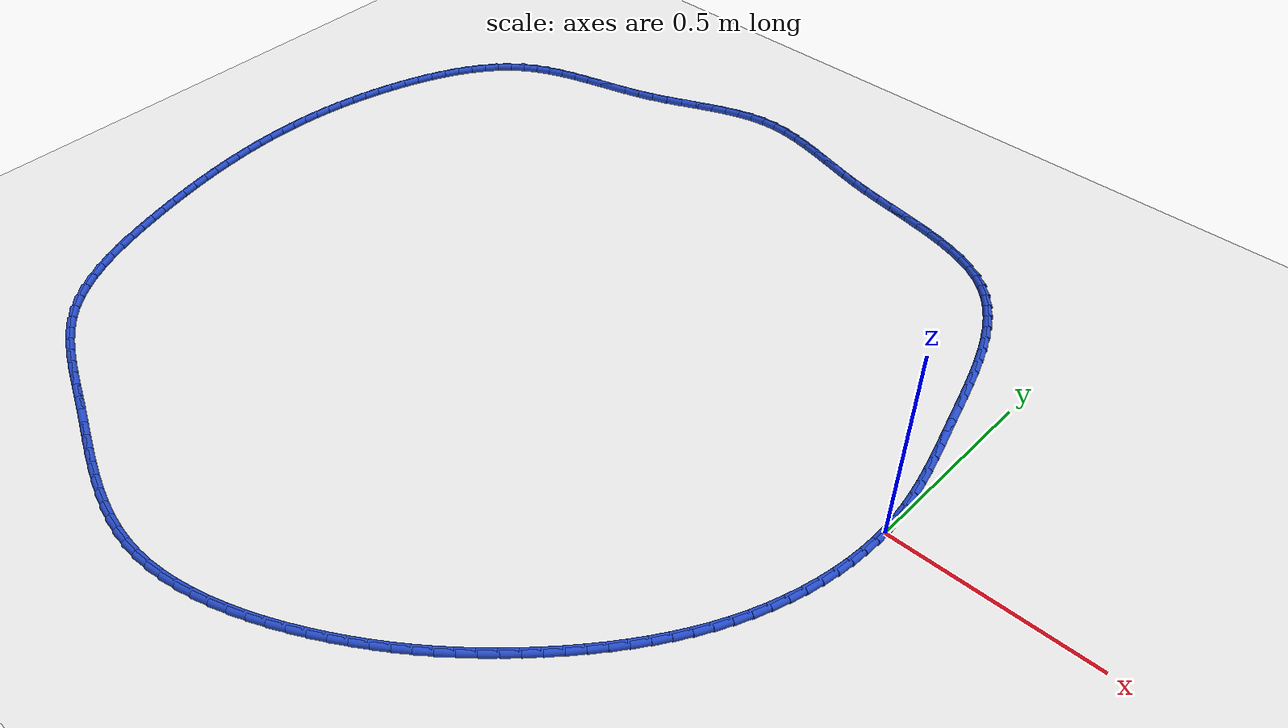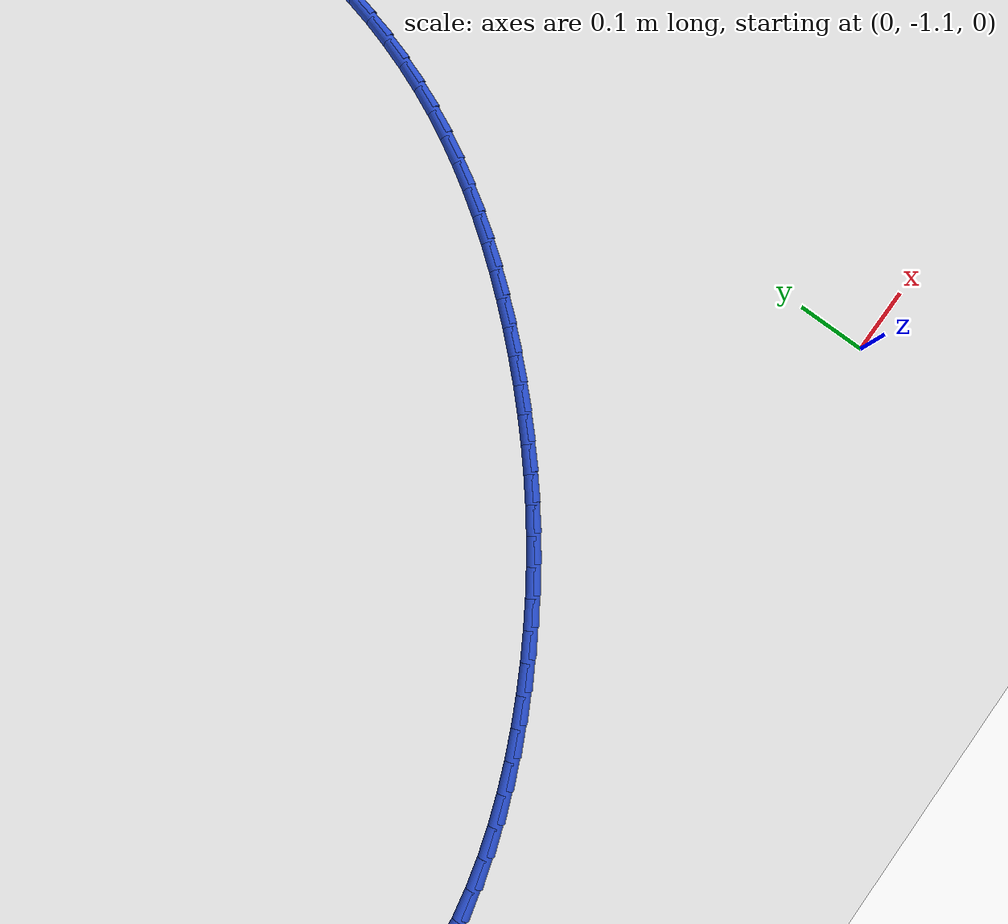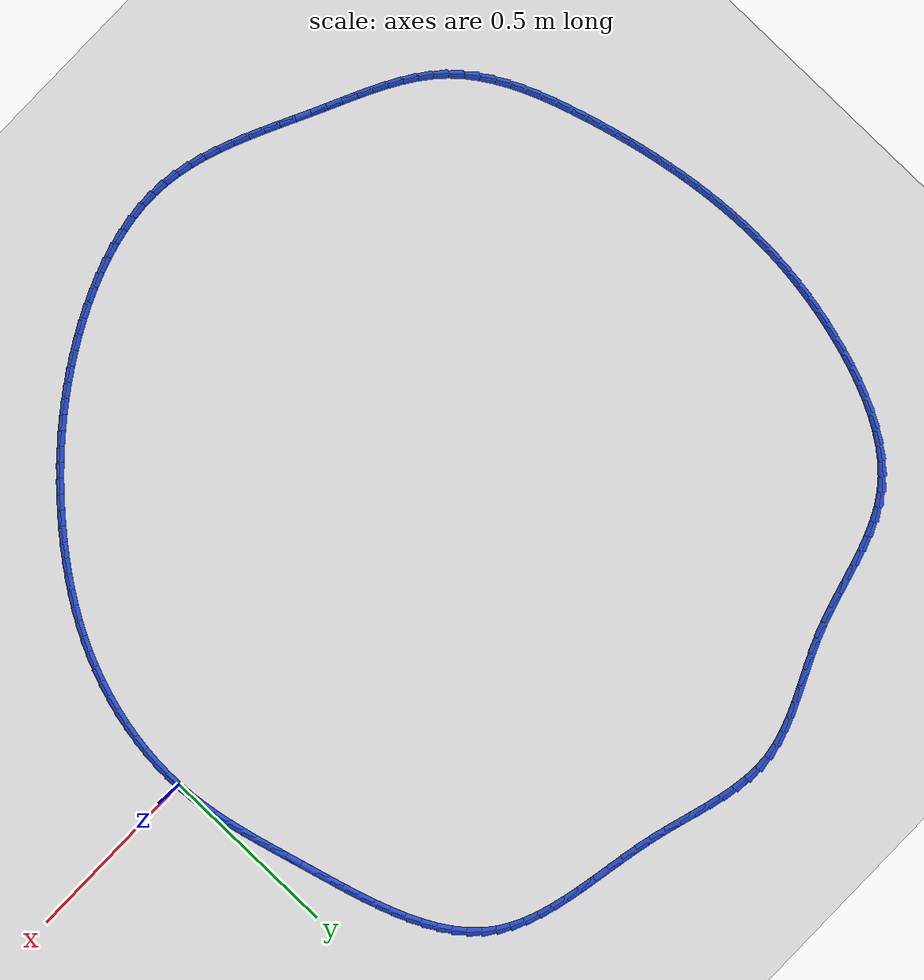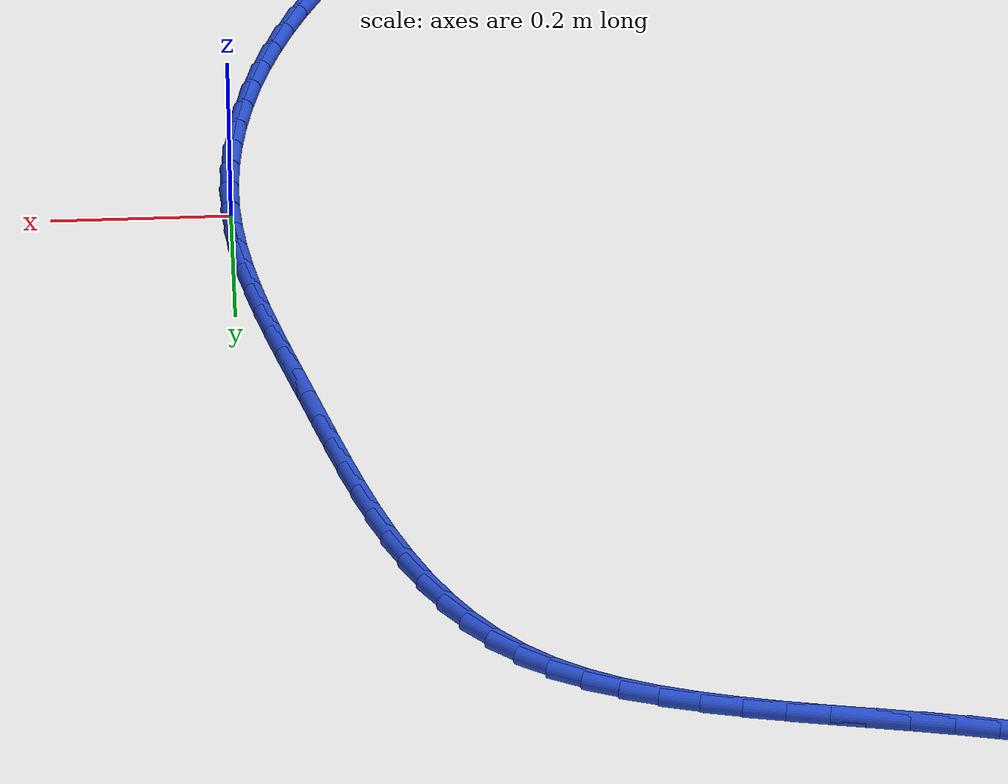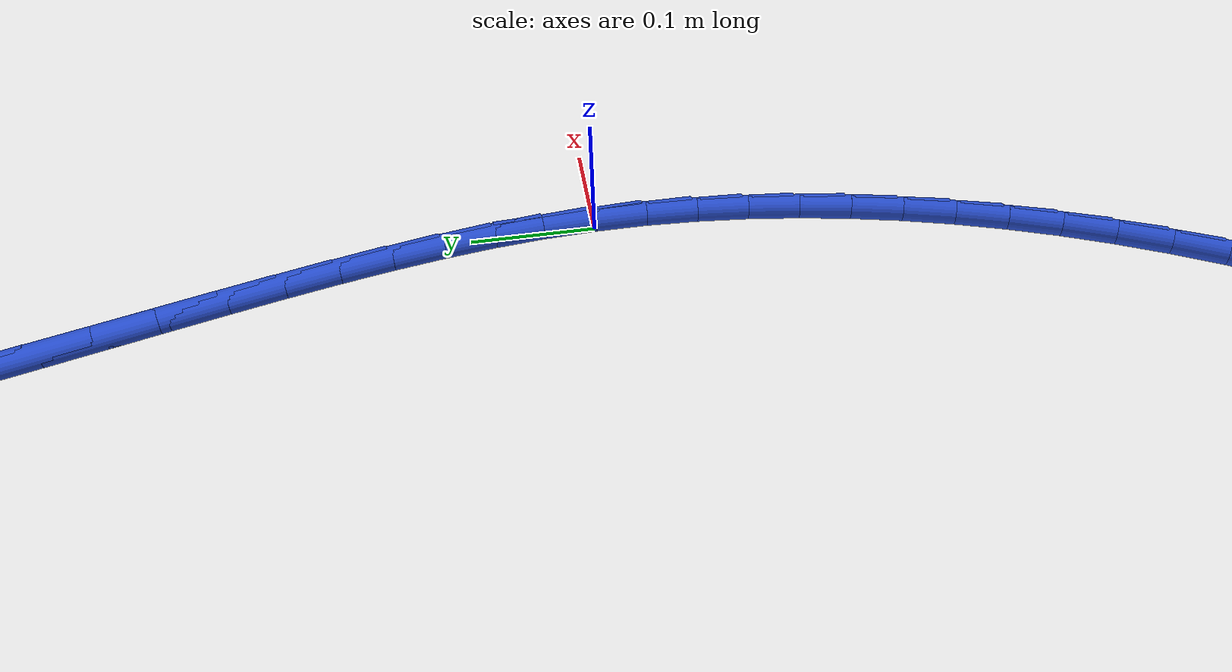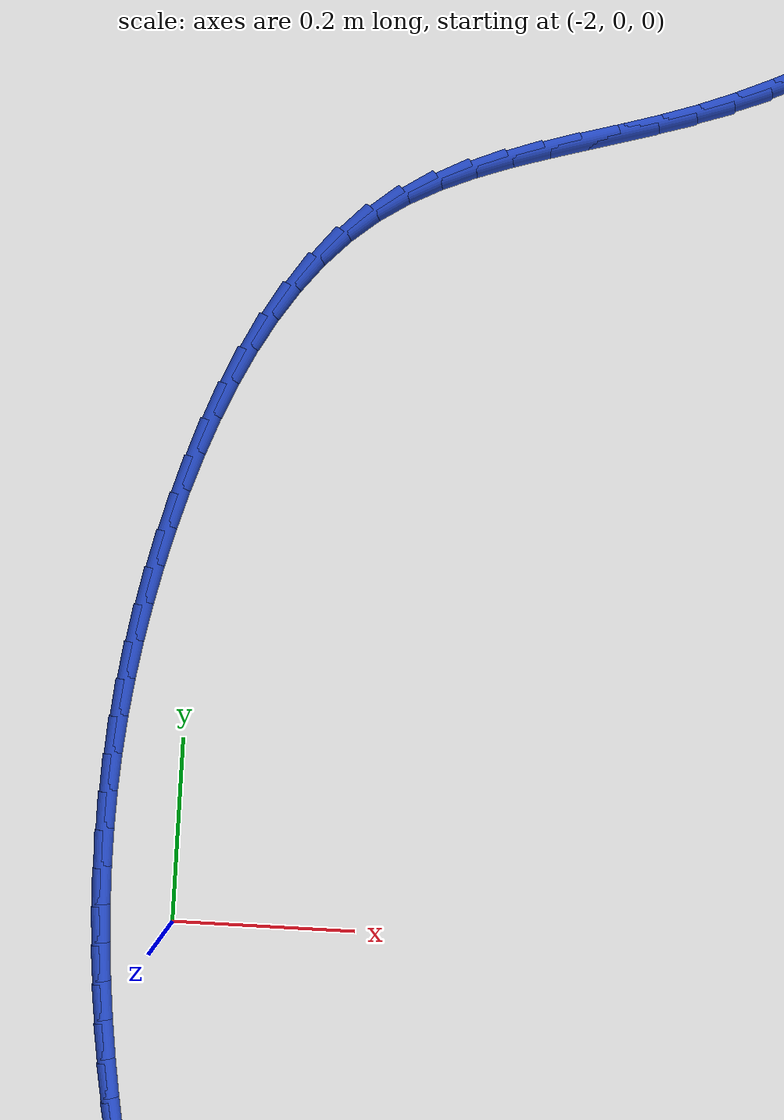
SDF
<sdf version="1.6">
 <world name="default">
  <light name="sun" type="directional">
   <pose>0 0 10 0 -0 0</pose>
   <diffuse>0.8 0.8 0.8 1</diffuse>
   <specular>0.2 0.2 0.2 1</specular>
   <attenuation>
    <range>1000</range>
    <constant>0.9</constant>
    <linear>0.01</linear>
    <quadratic>0.001</quadratic>
   </attenuation>
   <direction>-0.5 0.1 -0.9</direction>
  </light>
  <model name="ground_plane">
   <static>1</static>
   <link name="link">
    <collision name="collision">
     <geometry><plane><normal>0 0 1</normal><size>100 100</size></plane></geometry>
     <surface><friction><ode><mu>100</mu><mu2>50</mu2></ode></friction></surface>
    </collision>
    <visual name="visual">
     <cast_shadows>0</cast_shadows>
     <geometry><plane><normal>0 0 1</normal><size>100 100</size></plane></geometry>
     <material>
      <script><uri>file://media/materials/scripts/gazebo.material</uri><name>Gazebo/WhiteGlow</name></script>
     </material>
    </visual>
   </link>
  </model>
  <gravity>0 0 -9.8</gravity>
  <magnetic_field>6e-06 2.3e-05 -4.2e-05</magnetic_field>
  <atmosphere type="adiabatic"/>
  <physics name="default_physics" default="0" type="ode">
   <max_step_size>0.001</max_step_size>
   <real_time_factor>1</real_time_factor>
   <real_time_update_rate>1000</real_time_update_rate>
  </physics>
  <scene><ambient>0.4 0.4 0.4 1</ambient><background>0.7 0.7 0.7 1</background><shadows>1</shadows></scene>
  <spherical_coordinates>
   <surface_model>EARTH_WGS84</surface_model>
   <latitude_deg>0</latitude_deg>
   <longitude_deg>0</longitude_deg>
   <elevation>0</elevation>
   <heading_deg>0</heading_deg>
  </spherical_coordinates>
  <model name="line">
   <link name="link_0">
    <pose>2.6020852139652106e-17 1.5959455978986625e-16 0.01 0 1.57 -1.5124819271053642</pose>
    <collision name="collision">
     <geometry><cylinder><radius>0.01</radius><length>0.08</length></cylinder></geometry>
    </collision>
    <visual name="visual">
     <material>
      <script><name>Gazebo/Blue</name><uri>file://media/materials/scripts/gazebo.material</uri></script>
     </material>
     <geometry><cylinder><radius>0.01</radius><length>0.08</length></cylinder></geometry>
    </visual>
   </link>
   <link name="link_1">
    <pose>-0.0023930297820890945 0.04099016066702728 0.01 0 1.57 -1.4640141417196577</pose>
    <collision name="collision">
     <geometry><cylinder><radius>0.01</radius><length>0.08</length></cylinder></geometry>
    </collision>
    <visual name="visual">
     <material>
      <script><name>Gazebo/Blue</name><uri>file://media/materials/scripts/gazebo.material</uri></script>
     </material>
     <geometry><cylinder><radius>0.01</radius><length>0.08</length></cylinder></geometry>
    </visual>
   </link>
   <link name="link_2">
    <pose>-0.0067553265607276205 0.0816870605255259 0.01 0 1.57 -1.4215754872500803</pose>
    <collision name="collision">
     <geometry><cylinder><radius>0.01</radius><length>0.08</length></cylinder></geometry>
    </collision>
    <visual name="visual">
     <material>
      <script><name>Gazebo/Blue</name><uri>file://media/materials/scripts/gazebo.material</uri></script>
     </material>
     <geometry><cylinder><radius>0.01</radius><length>0.08</length></cylinder></geometry>
    </visual>
   </link>
   <link name="link_3">
    <pose>-0.012848597226478048 0.12221744090637951 0.01 0 1.57 -1.3855924008493954</pose>
    <collision name="collision">
     <geometry><cylinder><radius>0.01</radius><length>0.08</length></cylinder></geometry>
    </collision>
    <visual name="visual">
     <material>
      <script><name>Gazebo/Blue</name><uri>file://media/materials/scripts/gazebo.material</uri></script>
     </material>
     <geometry><cylinder><radius>0.01</radius><length>0.08</length></cylinder></geometry>
    </visual>
   </link>
   <link name="link_4">
    <pose>-0.02043454866990284 0.16270804314047127 0.01 0 1.57 -1.356285536956008</pose>
    <collision name="collision">
     <geometry><cylinder><radius>0.01</radius><length>0.08</length></cylinder></geometry>
    </collision>
    <visual name="visual">
     <material>
      <script><name>Gazebo/Blue</name><uri>file://media/materials/scripts/gazebo.material</uri></script>
     </material>
     <geometry><cylinder><radius>0.01</radius><length>0.08</length></cylinder></geometry>
    </visual>
   </link>
   <link name="link_5">
    <pose>-0.029274887781564455 0.20328560855868466 0.01 0 1.57 -1.3337097857130946</pose>
    <collision name="collision">
     <geometry><cylinder><radius>0.01</radius><length>0.08</length></cylinder></geometry>
    </collision>
    <visual name="visual">
     <material>
      <script><name>Gazebo/Blue</name><uri>file://media/materials/scripts/gazebo.material</uri></script>
     </material>
     <geometry><cylinder><radius>0.01</radius><length>0.08</length></cylinder></geometry>
    </visual>
   </link>
   <link name="link_6">
    <pose>-0.0391313214520254 0.24407687849190307 0.01 0 1.57 -1.3177953655166155</pose>
    <collision name="collision">
     <geometry><cylinder><radius>0.01</radius><length>0.08</length></cylinder></geometry>
    </collision>
    <visual name="visual">
     <material>
      <script><name>Gazebo/Blue</name><uri>file://media/materials/scripts/gazebo.material</uri></script>
     </material>
     <geometry><cylinder><radius>0.01</radius><length>0.08</length></cylinder></geometry>
    </visual>
   </link>
   <link name="link_7">
    <pose>-0.04976555657184812 0.28520859427100975 0.01 0 1.57 -1.3083835901399055</pose>
    <collision name="collision">
     <geometry><cylinder><radius>0.01</radius><length>0.08</length></cylinder></geometry>
    </collision>
    <visual name="visual">
     <material>
      <script><name>Gazebo/Blue</name><uri>file://media/materials/scripts/gazebo.material</uri></script>
     </material>
     <geometry><cylinder><radius>0.01</radius><length>0.08</length></cylinder></geometry>
    </visual>
   </link>
   <link name="link_8">
    <pose>-0.06093930003159509 0.32680749722688807 0.01 0 1.57 -1.305254239659153</pose>
    <collision name="collision">
     <geometry><cylinder><radius>0.01</radius><length>0.08</length></cylinder></geometry>
    </collision>
    <visual name="visual">
     <material>
      <script><name>Gazebo/Blue</name><uri>file://media/materials/scripts/gazebo.material</uri></script>
     </material>
     <geometry><cylinder><radius>0.01</radius><length>0.08</length></cylinder></geometry>
    </visual>
   </link>
   <link name="link_9">
    <pose>-0.0724142587218288 0.36900032869042143 0.01 0 1.57 -1.3074455239687846</pose>
    <collision name="collision">
     <geometry><cylinder><radius>0.01</radius><length>0.08</length></cylinder></geometry>
    </collision>
    <visual name="visual">
     <material>
      <script><name>Gazebo/Blue</name><uri>file://media/materials/scripts/gazebo.material</uri></script>
     </material>
     <geometry><cylinder><radius>0.01</radius><length>0.08</length></cylinder></geometry>
    </visual>
   </link>
   <link name="link_10">
    <pose>-0.08397723339862287 0.41188768243456314 0.01 0 1.57 -1.3070664677826795</pose>
    <collision name="collision">
     <geometry><cylinder><radius>0.01</radius><length>0.08</length></cylinder></geometry>
    </collision>
    <visual name="visual">
     <material>
      <script><name>Gazebo/Blue</name><uri>file://media/materials/scripts/gazebo.material</uri></script>
     </material>
     <geometry><cylinder><radius>0.01</radius><length>0.08</length></cylinder></geometry>
    </visual>
   </link>
   <link name="link_11">
    <pose>-0.09569388547635828 0.45527958220373976 0.01 0 1.57 -1.299430349507339</pose>
    <collision name="collision">
     <geometry><cylinder><radius>0.01</radius><length>0.08</length></cylinder></geometry>
    </collision>
    <visual name="visual">
     <material>
      <script><name>Gazebo/Blue</name><uri>file://media/materials/scripts/gazebo.material</uri></script>
     </material>
     <geometry><cylinder><radius>0.01</radius><length>0.08</length></cylinder></geometry>
    </visual>
   </link>
   <link name="link_12">
    <pose>-0.10780386450942175 0.49880475783339895 0.01 0 1.57 -1.2844283589881462</pose>
    <collision name="collision">
     <geometry><cylinder><radius>0.01</radius><length>0.08</length></cylinder></geometry>
    </collision>
    <visual name="visual">
     <material>
      <script><name>Gazebo/Blue</name><uri>file://media/materials/scripts/gazebo.material</uri></script>
     </material>
     <geometry><cylinder><radius>0.01</radius><length>0.08</length></cylinder></geometry>
    </visual>
   </link>
   <link name="link_13">
    <pose>-0.12054946503932609 0.5420891831087467 0.01 0 1.57 -1.2617476785269812</pose>
    <collision name="collision">
     <geometry><cylinder><radius>0.01</radius><length>0.08</length></cylinder></geometry>
    </collision>
    <visual name="visual">
     <material>
      <script><name>Gazebo/Blue</name><uri>file://media/materials/scripts/gazebo.material</uri></script>
     </material>
     <geometry><cylinder><radius>0.01</radius><length>0.08</length></cylinder></geometry>
    </visual>
   </link>
   <link name="link_14">
    <pose>-0.13417298160758426 0.5847588318149887 0.01 0 1.57 -1.2308032604516916</pose>
    <collision name="collision">
     <geometry><cylinder><radius>0.01</radius><length>0.08</length></cylinder></geometry>
    </collision>
    <visual name="visual">
     <material>
      <script><name>Gazebo/Blue</name><uri>file://media/materials/scripts/gazebo.material</uri></script>
     </material>
     <geometry><cylinder><radius>0.01</radius><length>0.08</length></cylinder></geometry>
    </visual>
   </link>
   <link name="link_15">
    <pose>-0.14891670875570912 0.6264396777373312 0.01 0 1.57 -1.1907385012193743</pose>
    <collision name="collision">
     <geometry><cylinder><radius>0.01</radius><length>0.08</length></cylinder></geometry>
    </collision>
    <visual name="visual">
     <material>
      <script><name>Gazebo/Blue</name><uri>file://media/materials/scripts/gazebo.material</uri></script>
     </material>
     <geometry><cylinder><radius>0.01</radius><length>0.08</length></cylinder></geometry>
    </visual>
   </link>
   <link name="link_16">
    <pose>-0.16502294102521364 0.6667576946609803 0.01 0 1.57 -1.1404344706703422</pose>
    <collision name="collision">
     <geometry><cylinder><radius>0.01</radius><length>0.08</length></cylinder></geometry>
    </collision>
    <visual name="visual">
     <material>
      <script><name>Gazebo/Blue</name><uri>file://media/materials/scripts/gazebo.material</uri></script>
     </material>
     <geometry><cylinder><radius>0.01</radius><length>0.08</length></cylinder></geometry>
    </visual>
   </link>
   <link name="link_17">
    <pose>-0.1827339729576107 0.705338856371142 0.01 0 1.57 -1.0785510076083233</pose>
    <collision name="collision">
     <geometry><cylinder><radius>0.01</radius><length>0.08</length></cylinder></geometry>
    </collision>
    <visual name="visual">
     <material>
      <script><name>Gazebo/Blue</name><uri>file://media/materials/scripts/gazebo.material</uri></script>
     </material>
     <geometry><cylinder><radius>0.01</radius><length>0.08</length></cylinder></geometry>
    </visual>
   </link>
   <link name="link_18">
    <pose>-0.2022920990944132 0.7418091366530223 0.01 0 1.57 -1.003638735944168</pose>
    <collision name="collision">
     <geometry><cylinder><radius>0.01</radius><length>0.08</length></cylinder></geometry>
    </collision>
    <visual name="visual">
     <material>
      <script><name>Gazebo/Blue</name><uri>file://media/materials/scripts/gazebo.material</uri></script>
     </material>
     <geometry><cylinder><radius>0.01</radius><length>0.08</length></cylinder></geometry>
    </visual>
   </link>
   <link name="link_19">
    <pose>-0.22393961397713405 0.7757945092918269 0.01 0 1.57 -0.91437884679505</pose>
    <collision name="collision">
     <geometry><cylinder><radius>0.01</radius><length>0.08</length></cylinder></geometry>
    </collision>
    <visual name="visual">
     <material>
      <script><name>Gazebo/Blue</name><uri>file://media/materials/scripts/gazebo.material</uri></script>
     </material>
     <geometry><cylinder><radius>0.01</radius><length>0.08</length></cylinder></geometry>
    </visual>
   </link>
   <link name="link_20">
    <pose>-0.24791881214728617 0.8069209480727625 0.01 0 1.57 -0.8100099982178355</pose>
    <collision name="collision">
     <geometry><cylinder><radius>0.01</radius><length>0.08</length></cylinder></geometry>
    </collision>
    <visual name="visual">
     <material>
      <script><name>Gazebo/Blue</name><uri>file://media/materials/scripts/gazebo.material</uri></script>
     </material>
     <geometry><cylinder><radius>0.01</radius><length>0.08</length></cylinder></geometry>
    </visual>
   </link>
   <link name="link_21">
    <pose>-0.2744719881463824 0.8348144267810342 0.01 0 1.57 -0.6911137265941127</pose>
    <collision name="collision">
     <geometry><cylinder><radius>0.01</radius><length>0.08</length></cylinder></geometry>
    </collision>
    <visual name="visual">
     <material>
      <script><name>Gazebo/Blue</name><uri>file://media/materials/scripts/gazebo.material</uri></script>
     </material>
     <geometry><cylinder><radius>0.01</radius><length>0.08</length></cylinder></geometry>
    </visual>
   </link>
   <link name="link_22">
    <pose>-0.3038379466848645 0.8591062473119588 0.01 0 1.57 -0.5697508326299255</pose>
    <collision name="collision">
     <geometry><cylinder><radius>0.01</radius><length>0.08</length></cylinder></geometry>
    </collision>
    <visual name="visual">
     <material>
      <script><name>Gazebo/Blue</name><uri>file://media/materials/scripts/gazebo.material</uri></script>
     </material>
     <geometry><cylinder><radius>0.01</radius><length>0.08</length></cylinder></geometry>
    </visual>
   </link>
   <link name="link_23">
    <pose>-0.33604981969480857 0.8797417230953111 0.01 0 1.57 -0.4641261025381618</pose>
    <collision name="collision">
     <geometry><cylinder><radius>0.01</radius><length>0.08</length></cylinder></geometry>
    </collision>
    <visual name="visual">
     <material>
      <script><name>Gazebo/Blue</name><uri>file://media/materials/scripts/gazebo.material</uri></script>
     </material>
     <geometry><cylinder><radius>0.01</radius><length>0.08</length></cylinder></geometry>
    </visual>
   </link>
   <link name="link_24">
    <pose>-0.37082406545335145 0.8971496500182978 0.01 0 1.57 -0.37677454660641013</pose>
    <collision name="collision">
     <geometry><cylinder><radius>0.01</radius><length>0.08</length></cylinder></geometry>
    </collision>
    <visual name="visual">
     <material>
      <script><name>Gazebo/Blue</name><uri>file://media/materials/scripts/gazebo.material</uri></script>
     </material>
     <geometry><cylinder><radius>0.01</radius><length>0.08</length></cylinder></geometry>
    </visual>
   </link>
   <link name="link_25">
    <pose>-0.4078501476765967 0.9118000379955692 0.01 0 1.57 -0.30721705196408294</pose>
    <collision name="collision">
     <geometry><cylinder><radius>0.01</radius><length>0.08</length></cylinder></geometry>
    </collision>
    <visual name="visual">
     <material>
      <script><name>Gazebo/Blue</name><uri>file://media/materials/scripts/gazebo.material</uri></script>
     </material>
     <geometry><cylinder><radius>0.01</radius><length>0.08</length></cylinder></geometry>
    </visual>
   </link>
   <link name="link_26">
    <pose>-0.4468175300806486 0.9241628969417752 0.01 0 1.57 -0.25413321259993166</pose>
    <collision name="collision">
     <geometry><cylinder><radius>0.01</radius><length>0.08</length></cylinder></geometry>
    </collision>
    <visual name="visual">
     <material>
      <script><name>Gazebo/Blue</name><uri>file://media/materials/scripts/gazebo.material</uri></script>
     </material>
     <geometry><cylinder><radius>0.01</radius><length>0.08</length></cylinder></geometry>
    </visual>
   </link>
   <link name="link_27">
    <pose>-0.48741567638161065 0.9347082367715663 0.01 0 1.57 -0.2159993130425771</pose>
    <collision name="collision">
     <geometry><cylinder><radius>0.01</radius><length>0.08</length></cylinder></geometry>
    </collision>
    <visual name="visual">
     <material>
      <script><name>Gazebo/Blue</name><uri>file://media/materials/scripts/gazebo.material</uri></script>
     </material>
     <geometry><cylinder><radius>0.01</radius><length>0.08</length></cylinder></geometry>
    </visual>
   </link>
   <link name="link_28">
    <pose>-0.5293340502955868 0.9439060673995924 0.01 0 1.57 -0.1914465601224357</pose>
    <collision name="collision">
     <geometry><cylinder><radius>0.01</radius><length>0.08</length></cylinder></geometry>
    </collision>
    <visual name="visual">
     <material>
      <script><name>Gazebo/Blue</name><uri>file://media/materials/scripts/gazebo.material</uri></script>
     </material>
     <geometry><cylinder><radius>0.01</radius><length>0.08</length></cylinder></geometry>
    </visual>
   </link>
   <link name="link_29">
    <pose>-0.5722621155386809 0.9522263987405043 0.01 0 1.57 -0.1794234652682764</pose>
    <collision name="collision">
     <geometry><cylinder><radius>0.01</radius><length>0.08</length></cylinder></geometry>
    </collision>
    <visual name="visual">
     <material>
      <script><name>Gazebo/Blue</name><uri>file://media/materials/scripts/gazebo.material</uri></script>
     </material>
     <geometry><cylinder><radius>0.01</radius><length>0.08</length></cylinder></geometry>
    </visual>
   </link>
   <link name="link_30">
    <pose>-0.6158893358269962 0.9601392407089515 0.01 0 1.57 -0.17924827015417547</pose>
    <collision name="collision">
     <geometry><cylinder><radius>0.01</radius><length>0.08</length></cylinder></geometry>
    </collision>
    <visual name="visual">
     <material>
      <script><name>Gazebo/Blue</name><uri>file://media/materials/scripts/gazebo.material</uri></script>
     </material>
     <geometry><cylinder><radius>0.01</radius><length>0.08</length></cylinder></geometry>
    </visual>
   </link>
   <link name="link_31">
    <pose>-0.6599051748766374 0.9681146032195846 0.01 0 1.57 -0.19060697666338466</pose>
    <collision name="collision">
     <geometry><cylinder><radius>0.01</radius><length>0.08</length></cylinder></geometry>
    </collision>
    <visual name="visual">
     <material>
      <script><name>Gazebo/Blue</name><uri>file://media/materials/scripts/gazebo.material</uri></script>
     </material>
     <geometry><cylinder><radius>0.01</radius><length>0.08</length></cylinder></geometry>
    </visual>
   </link>
   <link name="link_32">
    <pose>-0.7039990964037078 0.9766224961870537 0.01 0 1.57 -0.21352358582197672</pose>
    <collision name="collision">
     <geometry><cylinder><radius>0.01</radius><length>0.08</length></cylinder></geometry>
    </collision>
    <visual name="visual">
     <material>
      <script><name>Gazebo/Blue</name><uri>file://media/materials/scripts/gazebo.material</uri></script>
     </material>
     <geometry><cylinder><radius>0.01</radius><length>0.08</length></cylinder></geometry>
    </visual>
   </link>
   <link name="link_33">
    <pose>-0.7478605641243115 0.9861329295260091 0.01 0 1.57 -0.24641121918615122</pose>
    <collision name="collision">
     <geometry><cylinder><radius>0.01</radius><length>0.08</length></cylinder></geometry>
    </collision>
    <visual name="visual">
     <material>
      <script><name>Gazebo/Blue</name><uri>file://media/materials/scripts/gazebo.material</uri></script>
     </material>
     <geometry><cylinder><radius>0.01</radius><length>0.08</length></cylinder></geometry>
    </visual>
   </link>
   <link name="link_34">
    <pose>-0.7912015526779894 0.9970341692646006 0.01 0 1.57 -0.27240722136775364</pose>
    <collision name="collision">
     <geometry><cylinder><radius>0.01</radius><length>0.08</length></cylinder></geometry>
    </collision>
    <visual name="visual">
     <material>
      <script><name>Gazebo/Blue</name><uri>file://media/materials/scripts/gazebo.material</uri></script>
     </material>
     <geometry><cylinder><radius>0.01</radius><length>0.08</length></cylinder></geometry>
    </visual>
   </link>
   <link name="link_35">
    <pose>-0.8339382994603632 1.0089727423550356 0.01 0 1.57 -0.2822925483893574</pose>
    <collision name="collision">
     <geometry><cylinder><radius>0.01</radius><length>0.08</length></cylinder></geometry>
    </collision>
    <visual name="visual">
     <material>
      <script><name>Gazebo/Blue</name><uri>file://media/materials/scripts/gazebo.material</uri></script>
     </material>
     <geometry><cylinder><radius>0.01</radius><length>0.08</length></cylinder></geometry>
    </visual>
   </link>
   <link name="link_36">
    <pose>-0.8760958559954481 1.0212000391490306 0.01 0 1.57 -0.2755586525148894</pose>
    <collision name="collision">
     <geometry><cylinder><radius>0.01</radius><length>0.08</length></cylinder></geometry>
    </collision>
    <visual name="visual">
     <material>
      <script><name>Gazebo/Blue</name><uri>file://media/materials/scripts/gazebo.material</uri></script>
     </material>
     <geometry><cylinder><radius>0.01</radius><length>0.08</length></cylinder></geometry>
    </visual>
   </link>
   <link name="link_37">
    <pose>-0.917700287608891 1.0329637685817805 0.01 0 1.57 -0.2513501246381686</pose>
    <collision name="collision">
     <geometry><cylinder><radius>0.01</radius><length>0.08</length></cylinder></geometry>
    </collision>
    <visual name="visual">
     <material>
      <script><name>Gazebo/Blue</name><uri>file://media/materials/scripts/gazebo.material</uri></script>
     </material>
     <geometry><cylinder><radius>0.01</radius><length>0.08</length></cylinder></geometry>
    </visual>
   </link>
   <link name="link_38">
    <pose>-0.9587776596263371 1.0435116395884798 0.01 0 1.57 -0.208376921821317</pose>
    <collision name="collision">
     <geometry><cylinder><radius>0.01</radius><length>0.08</length></cylinder></geometry>
    </collision>
    <visual name="visual">
     <material>
      <script><name>Gazebo/Blue</name><uri>file://media/materials/scripts/gazebo.material</uri></script>
     </material>
     <geometry><cylinder><radius>0.01</radius><length>0.08</length></cylinder></geometry>
    </visual>
   </link>
   <link name="link_39">
    <pose>-0.9993540373734332 1.0520913611043234 0.01 0 1.57 -0.14508481558833924</pose>
    <collision name="collision">
     <geometry><cylinder><radius>0.01</radius><length>0.08</length></cylinder></geometry>
    </collision>
    <visual name="visual">
     <material>
      <script><name>Gazebo/Blue</name><uri>file://media/materials/scripts/gazebo.material</uri></script>
     </material>
     <geometry><cylinder><radius>0.01</radius><length>0.08</length></cylinder></geometry>
    </visual>
   </link>
   <link name="link_40">
    <pose>-1.0394554861758254 1.057950642064506 0.01 0 1.57 -0.060113959469717274</pose>
    <collision name="collision">
     <geometry><cylinder><radius>0.01</radius><length>0.08</length></cylinder></geometry>
    </collision>
    <visual name="visual">
     <material>
      <script><name>Gazebo/Blue</name><uri>file://media/materials/scripts/gazebo.material</uri></script>
     </material>
     <geometry><cylinder><radius>0.01</radius><length>0.08</length></cylinder></geometry>
    </visual>
   </link>
   <link name="link_41">
    <pose>-1.0791080713591603 1.0603371914042226 0.01 0 1.57 0.04682995415215745</pose>
    <collision name="collision">
     <geometry><cylinder><radius>0.01</radius><length>0.08</length></cylinder></geometry>
    </collision>
    <visual name="visual">
     <material>
      <script><name>Gazebo/Blue</name><uri>file://media/materials/scripts/gazebo.material</uri></script>
     </material>
     <geometry><cylinder><radius>0.01</radius><length>0.08</length></cylinder></geometry>
    </visual>
   </link>
   <link name="link_42">
    <pose>-1.118337858254652 1.0584987181346814 0.01 0 1.57 0.1668381147046109</pose>
    <collision name="collision">
     <geometry><cylinder><radius>0.01</radius><length>0.08</length></cylinder></geometry>
    </collision>
    <visual name="visual">
     <material>
      <script><name>Gazebo/Blue</name><uri>file://media/materials/scripts/gazebo.material</uri></script>
     </material>
     <geometry><cylinder><radius>0.01</radius><length>0.08</length></cylinder></geometry>
    </visual>
   </link>
   <link name="link_43">
    <pose>-1.1571908975851775 1.0519557294137283 0.01 0 1.57 0.2693754659259627</pose>
    <collision name="collision">
     <geometry><cylinder><radius>0.01</radius><length>0.08</length></cylinder></geometry>
    </collision>
    <visual name="visual">
     <material>
      <script><name>Gazebo/Blue</name><uri>file://media/materials/scripts/gazebo.material</uri></script>
     </material>
     <geometry><cylinder><radius>0.01</radius><length>0.08</length></cylinder></geometry>
    </visual>
   </link>
   <link name="link_44">
    <pose>-1.1957916204412364 1.0412986148104966 0.01 0 1.57 0.3469685080968289</pose>
    <collision name="collision">
     <geometry><cylinder><radius>0.01</radius><length>0.08</length></cylinder></geometry>
    </collision>
    <visual name="visual">
     <material>
      <script><name>Gazebo/Blue</name><uri>file://media/materials/scripts/gazebo.material</uri></script>
     </material>
     <geometry><cylinder><radius>0.01</radius><length>0.08</length></cylinder></geometry>
    </visual>
   </link>
   <link name="link_45">
    <pose>-1.234283670298164 1.0273800105923496 0.01 0 1.57 0.40084733627559416</pose>
    <collision name="collision">
     <geometry><cylinder><radius>0.01</radius><length>0.08</length></cylinder></geometry>
    </collision>
    <visual name="visual">
     <material>
      <script><name>Gazebo/Blue</name><uri>file://media/materials/scripts/gazebo.material</uri></script>
     </material>
     <geometry><cylinder><radius>0.01</radius><length>0.08</length></cylinder></geometry>
    </visual>
   </link>
   <link name="link_46">
    <pose>-1.272810690631298 1.0110525530266525 0.01 0 1.57 0.432823786957801</pose>
    <collision name="collision">
     <geometry><cylinder><radius>0.01</radius><length>0.08</length></cylinder></geometry>
    </collision>
    <visual name="visual">
     <material>
      <script><name>Gazebo/Blue</name><uri>file://media/materials/scripts/gazebo.material</uri></script>
     </material>
     <geometry><cylinder><radius>0.01</radius><length>0.08</length></cylinder></geometry>
    </visual>
   </link>
   <link name="link_47">
    <pose>-1.311516324915974 0.9931688783807696 0.01 0 1.57 0.4444723672704669</pose>
    <collision name="collision">
     <geometry><cylinder><radius>0.01</radius><length>0.08</length></cylinder></geometry>
    </collision>
    <visual name="visual">
     <material>
      <script><name>Gazebo/Blue</name><uri>file://media/materials/scripts/gazebo.material</uri></script>
     </material>
     <geometry><cylinder><radius>0.01</radius><length>0.08</length></cylinder></geometry>
    </visual>
   </link>
   <link name="link_48">
    <pose>-1.3505442166275285 0.974581622922065 0.01 0 1.57 0.43678856787306714</pose>
    <collision name="collision">
     <geometry><cylinder><radius>0.01</radius><length>0.08</length></cylinder></geometry>
    </collision>
    <visual name="visual">
     <material>
      <script><name>Gazebo/Blue</name><uri>file://media/materials/scripts/gazebo.material</uri></script>
     </material>
     <geometry><cylinder><radius>0.01</radius><length>0.08</length></cylinder></geometry>
    </visual>
   </link>
   <link name="link_49">
    <pose>-1.390038009241298 0.9561434229179036 0.01 0 1.57 0.41013310359204996</pose>
    <collision name="collision">
     <geometry><cylinder><radius>0.01</radius><length>0.08</length></cylinder></geometry>
    </collision>
    <visual name="visual">
     <material>
      <script><name>Gazebo/Blue</name><uri>file://media/materials/scripts/gazebo.material</uri></script>
     </material>
     <geometry><cylinder><radius>0.01</radius><length>0.08</length></cylinder></geometry>
    </visual>
   </link>
   <link name="link_50">
    <pose>-1.4301413462326187 0.9387069146356495 0.01 0 1.57 0.36523144877931446</pose>
    <collision name="collision">
     <geometry><cylinder><radius>0.01</radius><length>0.08</length></cylinder></geometry>
    </collision>
    <visual name="visual">
     <material>
      <script><name>Gazebo/Blue</name><uri>file://media/materials/scripts/gazebo.material</uri></script>
     </material>
     <geometry><cylinder><radius>0.01</radius><length>0.08</length></cylinder></geometry>
    </visual>
   </link>
   <link name="link_51">
    <pose>-1.4709856224677897 0.9230885810543774 0.01 0 1.57 0.3196486616883416</pose>
    <collision name="collision">
     <geometry><cylinder><radius>0.01</radius><length>0.08</length></cylinder></geometry>
    </collision>
    <visual name="visual">
     <material>
      <script><name>Gazebo/Blue</name><uri>file://media/materials/scripts/gazebo.material</uri></script>
     </material>
     <geometry><cylinder><radius>0.01</radius><length>0.08</length></cylinder></geometry>
    </visual>
   </link>
   <link name="link_52">
    <pose>-1.5124510610120458 0.9093635404393231 0.01 0 1.57 0.2899536279049206</pose>
    <collision name="collision">
     <geometry><cylinder><radius>0.01</radius><length>0.08</length></cylinder></geometry>
    </collision>
    <visual name="visual">
     <material>
      <script><name>Gazebo/Blue</name><uri>file://media/materials/scripts/gazebo.material</uri></script>
     </material>
     <geometry><cylinder><radius>0.01</radius><length>0.08</length></cylinder></geometry>
    </visual>
   </link>
   <link name="link_53">
    <pose>-1.5541825952830777 0.896912424487231 0.01 0 1.57 0.27670096728061605</pose>
    <collision name="collision">
     <geometry><cylinder><radius>0.01</radius><length>0.08</length></cylinder></geometry>
    </collision>
    <visual name="visual">
     <material>
      <script><name>Gazebo/Blue</name><uri>file://media/materials/scripts/gazebo.material</uri></script>
     </material>
     <geometry><cylinder><radius>0.01</radius><length>0.08</length></cylinder></geometry>
    </visual>
   </link>
   <link name="link_54">
    <pose>-1.595816090769394 0.8850890997775329 0.01 0 1.57 0.2800600114164097</pose>
    <collision name="collision">
     <geometry><cylinder><radius>0.01</radius><length>0.08</length></cylinder></geometry>
    </collision>
    <visual name="visual">
     <material>
      <script><name>Gazebo/Blue</name><uri>file://media/materials/scripts/gazebo.material</uri></script>
     </material>
     <geometry><cylinder><radius>0.01</radius><length>0.08</length></cylinder></geometry>
    </visual>
   </link>
   <link name="link_55">
    <pose>-1.636987412959505 0.87324743288966 0.01 0 1.57 0.30058730874194656</pose>
    <collision name="collision">
     <geometry><cylinder><radius>0.01</radius><length>0.08</length></cylinder></geometry>
    </collision>
    <visual name="visual">
     <material>
      <script><name>Gazebo/Blue</name><uri>file://media/materials/scripts/gazebo.material</uri></script>
     </material>
     <geometry><cylinder><radius>0.01</radius><length>0.08</length></cylinder></geometry>
    </visual>
   </link>
   <link name="link_56">
    <pose>-1.6773324273419223 0.8607412904030437 0.01 0 1.57 0.3392356269195323</pose>
    <collision name="collision">
     <geometry><cylinder><radius>0.01</radius><length>0.08</length></cylinder></geometry>
    </collision>
    <visual name="visual">
     <material>
      <script><name>Gazebo/Blue</name><uri>file://media/materials/scripts/gazebo.material</uri></script>
     </material>
     <geometry><cylinder><radius>0.01</radius><length>0.08</length></cylinder></geometry>
    </visual>
   </link>
   <link name="link_57">
    <pose>-1.7164869994051548 0.8469245388971158 0.01 0 1.57 0.39720958319567645</pose>
    <collision name="collision">
     <geometry><cylinder><radius>0.01</radius><length>0.08</length></cylinder></geometry>
    </collision>
    <visual name="visual">
     <material>
      <script><name>Gazebo/Blue</name><uri>file://media/materials/scripts/gazebo.material</uri></script>
     </material>
     <geometry><cylinder><radius>0.01</radius><length>0.08</length></cylinder></geometry>
    </visual>
   </link>
   <link name="link_58">
    <pose>-1.7540869946377127 0.831151044951307 0.01 0 1.57 0.47558673866967077</pose>
    <collision name="collision">
     <geometry><cylinder><radius>0.01</radius><length>0.08</length></cylinder></geometry>
    </collision>
    <visual name="visual">
     <material>
      <script><name>Gazebo/Blue</name><uri>file://media/materials/scripts/gazebo.material</uri></script>
     </material>
     <geometry><cylinder><radius>0.01</radius><length>0.08</length></cylinder></geometry>
    </visual>
   </link>
   <link name="link_59">
    <pose>-1.7897682785281068 0.8127746751450495 0.01 0 1.57 0.5746134322527496</pose>
    <collision name="collision">
     <geometry><cylinder><radius>0.01</radius><length>0.08</length></cylinder></geometry>
    </collision>
    <visual name="visual">
     <material>
      <script><name>Gazebo/Blue</name><uri>file://media/materials/scripts/gazebo.material</uri></script>
     </material>
     <geometry><cylinder><radius>0.01</radius><length>0.08</length></cylinder></geometry>
    </visual>
   </link>
   <link name="link_60">
    <pose>-1.8231667165648455 0.7911492960577742 0.01 0 1.57 0.6890913459508331</pose>
    <collision name="collision">
     <geometry><cylinder><radius>0.01</radius><length>0.08</length></cylinder></geometry>
    </collision>
    <visual name="visual">
     <material>
      <script><name>Gazebo/Blue</name><uri>file://media/materials/scripts/gazebo.material</uri></script>
     </material>
     <geometry><cylinder><radius>0.01</radius><length>0.08</length></cylinder></geometry>
    </visual>
   </link>
   <link name="link_61">
    <pose>-1.853980158669267 0.7657648854449245 0.01 0 1.57 0.7975878850034774</pose>
    <collision name="collision">
     <geometry><cylinder><radius>0.01</radius><length>0.08</length></cylinder></geometry>
    </collision>
    <visual name="visual">
     <material>
      <script><name>Gazebo/Blue</name><uri>file://media/materials/scripts/gazebo.material</uri></script>
     </material>
     <geometry><cylinder><radius>0.01</radius><length>0.08</length></cylinder></geometry>
    </visual>
   </link>
   <link name="link_62">
    <pose>-1.882228727913692 0.7368190983863492 0.01 0 1.57 0.893323602333009</pose>
    <collision name="collision">
     <geometry><cylinder><radius>0.01</radius><length>0.08</length></cylinder></geometry>
    </collision>
    <visual name="visual">
     <material>
      <script><name>Gazebo/Blue</name><uri>file://media/materials/scripts/gazebo.material</uri></script>
     </material>
     <geometry><cylinder><radius>0.01</radius><length>0.08</length></cylinder></geometry>
    </visual>
   </link>
   <link name="link_63">
    <pose>-1.908036956387296 0.7047388609808019 0.01 0 1.57 0.9768331360070919</pose>
    <collision name="collision">
     <geometry><cylinder><radius>0.01</radius><length>0.08</length></cylinder></geometry>
    </collision>
    <visual name="visual">
     <material>
      <script><name>Gazebo/Blue</name><uri>file://media/materials/scripts/gazebo.material</uri></script>
     </material>
     <geometry><cylinder><radius>0.01</radius><length>0.08</length></cylinder></geometry>
    </visual>
   </link>
   <link name="link_64">
    <pose>-1.9315294298668784 0.6699512172193091 0.01 0 1.57 1.0492215812812835</pose>
    <collision name="collision">
     <geometry><cylinder><radius>0.01</radius><length>0.08</length></cylinder></geometry>
    </collision>
    <visual name="visual">
     <material>
      <script><name>Gazebo/Blue</name><uri>file://media/materials/scripts/gazebo.material</uri></script>
     </material>
     <geometry><cylinder><radius>0.01</radius><length>0.08</length></cylinder></geometry>
    </visual>
   </link>
   <link name="link_65">
    <pose>-1.9528307341292395 0.6328832110928961 0.01 0 1.57 1.1118035574701328</pose>
    <collision name="collision">
     <geometry><cylinder><radius>0.01</radius><length>0.08</length></cylinder></geometry>
    </collision>
    <visual name="visual">
     <material>
      <script><name>Gazebo/Blue</name><uri>file://media/materials/scripts/gazebo.material</uri></script>
     </material>
     <geometry><cylinder><radius>0.01</radius><length>0.08</length></cylinder></geometry>
    </visual>
   </link>
   <link name="link_66">
    <pose>-1.9720654549511787 0.5939618865925883 0.01 0 1.57 1.1658857991225664</pose>
    <collision name="collision">
     <geometry><cylinder><radius>0.01</radius><length>0.08</length></cylinder></geometry>
    </collision>
    <visual name="visual">
     <material>
      <script><name>Gazebo/Blue</name><uri>file://media/materials/scripts/gazebo.material</uri></script>
     </material>
     <geometry><cylinder><radius>0.01</radius><length>0.08</length></cylinder></geometry>
    </visual>
   </link>
   <link name="link_67">
    <pose>-1.9893581781094956 0.5536142877094125 0.01 0 1.57 1.2126566142738422</pose>
    <collision name="collision">
     <geometry><cylinder><radius>0.01</radius><length>0.08</length></cylinder></geometry>
    </collision>
    <visual name="visual">
     <material>
      <script><name>Gazebo/Blue</name><uri>file://media/materials/scripts/gazebo.material</uri></script>
     </material>
     <geometry><cylinder><radius>0.01</radius><length>0.08</length></cylinder></geometry>
    </visual>
   </link>
   <link name="link_68">
    <pose>-2.004833489380991 0.5122674584343934 0.01 0 1.57 1.2531417944073582</pose>
    <collision name="collision">
     <geometry><cylinder><radius>0.01</radius><length>0.08</length></cylinder></geometry>
    </collision>
    <visual name="visual">
     <material>
      <script><name>Gazebo/Blue</name><uri>file://media/materials/scripts/gazebo.material</uri></script>
     </material>
     <geometry><cylinder><radius>0.01</radius><length>0.08</length></cylinder></geometry>
    </visual>
   </link>
   <link name="link_69">
    <pose>-2.0186159745424628 0.47034844275855753 0.01 0 1.57 1.2881959919582362</pose>
    <collision name="collision">
     <geometry><cylinder><radius>0.01</radius><length>0.08</length></cylinder></geometry>
    </collision>
    <visual name="visual">
     <material>
      <script><name>Gazebo/Blue</name><uri>file://media/materials/scripts/gazebo.material</uri></script>
     </material>
     <geometry><cylinder><radius>0.01</radius><length>0.08</length></cylinder></geometry>
    </visual>
   </link>
   <link name="link_70">
    <pose>-2.0308302193707117 0.4282842846729304 0.01 0 1.57 1.318961845787762</pose>
    <collision name="collision">
     <geometry><cylinder><radius>0.01</radius><length>0.08</length></cylinder></geometry>
    </collision>
    <visual name="visual">
     <material>
      <script><name>Gazebo/Blue</name><uri>file://media/materials/scripts/gazebo.material</uri></script>
     </material>
     <geometry><cylinder><radius>0.01</radius><length>0.08</length></cylinder></geometry>
    </visual>
   </link>
   <link name="link_71">
    <pose>-2.0415916009582786 0.3864595272017528 0.01 0 1.57 1.3491596279833953</pose>
    <collision name="collision">
     <geometry><cylinder><radius>0.01</radius><length>0.08</length></cylinder></geometry>
    </collision>
    <visual name="visual">
     <material>
      <script><name>Gazebo/Blue</name><uri>file://media/materials/scripts/gazebo.material</uri></script>
     </material>
     <geometry><cylinder><radius>0.01</radius><length>0.08</length></cylinder></geometry>
    </visual>
   </link>
   <link name="link_72">
    <pose>-2.0509469859283183 0.3449425160601024 0.01 0 1.57 1.3801950970127195</pose>
    <collision name="collision">
     <geometry><cylinder><radius>0.01</radius><length>0.08</length></cylinder></geometry>
    </collision>
    <visual name="visual">
     <material>
      <script><name>Gazebo/Blue</name><uri>file://media/materials/scripts/gazebo.material</uri></script>
     </material>
     <geometry><cylinder><radius>0.01</radius><length>0.08</length></cylinder></geometry>
    </visual>
   </link>
   <link name="link_73">
    <pose>-2.0589123563312772 0.3036590549709482 0.01 0 1.57 1.4118750400422657</pose>
    <collision name="collision">
     <geometry><cylinder><radius>0.01</radius><length>0.08</length></cylinder></geometry>
    </collision>
    <visual name="visual">
     <material>
      <script><name>Gazebo/Blue</name><uri>file://media/materials/scripts/gazebo.material</uri></script>
     </material>
     <geometry><cylinder><radius>0.01</radius><length>0.08</length></cylinder></geometry>
    </visual>
   </link>
   <link name="link_74">
    <pose>-2.065503544680629 0.2625342574972323 0.01 0 1.57 1.443977949198405</pose>
    <collision name="collision">
     <geometry><cylinder><radius>0.01</radius><length>0.08</length></cylinder></geometry>
    </collision>
    <visual name="visual">
     <material>
      <script><name>Gazebo/Blue</name><uri>file://media/materials/scripts/gazebo.material</uri></script>
     </material>
     <geometry><cylinder><radius>0.01</radius><length>0.08</length></cylinder></geometry>
    </visual>
   </link>
   <link name="link_75">
    <pose>-2.070736383489848 0.22149323720189537 0.01 0 1.57 1.4762673007500422</pose>
    <collision name="collision">
     <geometry><cylinder><radius>0.01</radius><length>0.08</length></cylinder></geometry>
    </collision>
    <visual name="visual">
     <material>
      <script><name>Gazebo/Blue</name><uri>file://media/materials/scripts/gazebo.material</uri></script>
     </material>
     <geometry><cylinder><radius>0.01</radius><length>0.08</length></cylinder></geometry>
    </visual>
   </link>
   <link name="link_76">
    <pose>-2.0746267052724097 0.18046110764787895 0.01 0 1.57 1.5084467003666089</pose>
    <collision name="collision">
     <geometry><cylinder><radius>0.01</radius><length>0.08</length></cylinder></geometry>
    </collision>
    <visual name="visual">
     <material>
      <script><name>Gazebo/Blue</name><uri>file://media/materials/scripts/gazebo.material</uri></script>
     </material>
     <geometry><cylinder><radius>0.01</radius><length>0.08</length></cylinder></geometry>
    </visual>
   </link>
   <link name="link_77">
    <pose>-2.077192117504785 0.13936884789929915 0.01 0 1.57 1.5398877108221358</pose>
    <collision name="collision">
     <geometry><cylinder><radius>0.01</radius><length>0.08</length></cylinder></geometry>
    </collision>
    <visual name="visual">
     <material>
      <script><name>Gazebo/Blue</name><uri>file://media/materials/scripts/gazebo.material</uri></script>
     </material>
     <geometry><cylinder><radius>0.01</radius><length>0.08</length></cylinder></geometry>
    </visual>
   </link>
   <link name="link_78">
    <pose>-2.0784651005523838 0.09819658562094903 0.01 0 1.57 1.5703004252039297</pose>
    <collision name="collision">
     <geometry><cylinder><radius>0.01</radius><length>0.08</length></cylinder></geometry>
    </collision>
    <visual name="visual">
     <material>
      <script><name>Gazebo/Blue</name><uri>file://media/materials/scripts/gazebo.material</uri></script>
     </material>
     <geometry><cylinder><radius>0.01</radius><length>0.08</length></cylinder></geometry>
    </visual>
   </link>
   <link name="link_79">
    <pose>-2.078485555312175 0.0569489701925229 0.01 0 1.57 -1.5419521567926375</pose>
    <collision name="collision">
     <geometry><cylinder><radius>0.01</radius><length>0.08</length></cylinder></geometry>
    </collision>
    <visual name="visual">
     <material>
      <script><name>Gazebo/Blue</name><uri>file://media/materials/scripts/gazebo.material</uri></script>
     </material>
     <geometry><cylinder><radius>0.01</radius><length>0.08</length></cylinder></geometry>
    </visual>
   </link>
   <link name="link_80">
    <pose>-2.077293437264896 0.015630831369964723 0.01 0 1.57 -1.5137168703543495</pose>
    <collision name="collision">
     <geometry><cylinder><radius>0.01</radius><length>0.08</length></cylinder></geometry>
    </collision>
    <visual name="visual">
     <material>
      <script><name>Gazebo/Blue</name><uri>file://media/materials/scripts/gazebo.material</uri></script>
     </material>
     <geometry><cylinder><radius>0.01</radius><length>0.08</length></cylinder></geometry>
    </visual>
   </link>
   <link name="link_81">
    <pose>-2.0749287018912854 -0.02575300109078106 0.01 0 1.57 -1.486608699585267</pose>
    <collision name="collision">
     <geometry><cylinder><radius>0.01</radius><length>0.08</length></cylinder></geometry>
    </collision>
    <visual name="visual">
     <material>
      <script><name>Gazebo/Blue</name><uri>file://media/materials/scripts/gazebo.material</uri></script>
     </material>
     <geometry><cylinder><radius>0.01</radius><length>0.08</length></cylinder></geometry>
    </visual>
   </link>
   <link name="link_82">
    <pose>-2.0714313046720814 -0.06719769743377096 0.01 0 1.57 -1.4606410888648518</pose>
    <collision name="collision">
     <geometry><cylinder><radius>0.01</radius><length>0.08</length></cylinder></geometry>
    </collision>
    <visual name="visual">
     <material>
      <script><name>Gazebo/Blue</name><uri>file://media/materials/scripts/gazebo.material</uri></script>
     </material>
     <geometry><cylinder><radius>0.01</radius><length>0.08</length></cylinder></geometry>
    </visual>
   </link>
   <link name="link_83">
    <pose>-2.0668412010880224 -0.1086984279030591 0.01 0 1.57 -1.4358195977456463</pose>
    <collision name="collision">
     <geometry><cylinder><radius>0.01</radius><length>0.08</length></cylinder></geometry>
    </collision>
    <visual name="visual">
     <material>
      <script><name>Gazebo/Blue</name><uri>file://media/materials/scripts/gazebo.material</uri></script>
     </material>
     <geometry><cylinder><radius>0.01</radius><length>0.08</length></cylinder></geometry>
    </visual>
   </link>
   <link name="link_84">
    <pose>-2.0611983466198462 -0.15025036274270184 0.01 0 1.57 -1.412142931347738</pose>
    <collision name="collision">
     <geometry><cylinder><radius>0.01</radius><length>0.08</length></cylinder></geometry>
    </collision>
    <visual name="visual">
     <material>
      <script><name>Gazebo/Blue</name><uri>file://media/materials/scripts/gazebo.material</uri></script>
     </material>
     <geometry><cylinder><radius>0.01</radius><length>0.08</length></cylinder></geometry>
    </visual>
   </link>
   <link name="link_85">
    <pose>-2.0545426967482925 -0.191848672196755 0.01 0 1.57 -1.3896039617541622</pose>
    <collision name="collision">
     <geometry><cylinder><radius>0.01</radius><length>0.08</length></cylinder></geometry>
    </collision>
    <visual name="visual">
     <material>
      <script><name>Gazebo/Blue</name><uri>file://media/materials/scripts/gazebo.material</uri></script>
     </material>
     <geometry><cylinder><radius>0.01</radius><length>0.08</length></cylinder></geometry>
    </visual>
   </link>
   <link name="link_86">
    <pose>-2.0469142069540984 -0.23348852650927407 0.01 0 1.57 -1.3681907109621316</pose>
    <collision name="collision">
     <geometry><cylinder><radius>0.01</radius><length>0.08</length></cylinder></geometry>
    </collision>
    <visual name="visual">
     <material>
      <script><name>Gazebo/Blue</name><uri>file://media/materials/scripts/gazebo.material</uri></script>
     </material>
     <geometry><cylinder><radius>0.01</radius><length>0.08</length></cylinder></geometry>
    </visual>
   </link>
   <link name="link_87">
    <pose>-2.038352832718002 -0.2751650959243156 0.01 0 1.57 -1.3478872741241679</pose>
    <collision name="collision">
     <geometry><cylinder><radius>0.01</radius><length>0.08</length></cylinder></geometry>
    </collision>
    <visual name="visual">
     <material>
      <script><name>Gazebo/Blue</name><uri>file://media/materials/scripts/gazebo.material</uri></script>
     </material>
     <geometry><cylinder><radius>0.01</radius><length>0.08</length></cylinder></geometry>
    </visual>
   </link>
   <link name="link_88">
    <pose>-2.028898529520742 -0.3168735506859336 0.01 0 1.57 -1.3286746690948457</pose>
    <collision name="collision">
     <geometry><cylinder><radius>0.01</radius><length>0.08</length></cylinder></geometry>
    </collision>
    <visual name="visual">
     <material>
      <script><name>Gazebo/Blue</name><uri>file://media/materials/scripts/gazebo.material</uri></script>
     </material>
     <geometry><cylinder><radius>0.01</radius><length>0.08</length></cylinder></geometry>
    </visual>
   </link>
   <link name="link_89">
    <pose>-2.0185912528430565 -0.3586090610381846 0.01 0 1.57 -1.310531604447224</pose>
    <collision name="collision">
     <geometry><cylinder><radius>0.01</radius><length>0.08</length></cylinder></geometry>
    </collision>
    <visual name="visual">
     <material>
      <script><name>Gazebo/Blue</name><uri>file://media/materials/scripts/gazebo.material</uri></script>
     </material>
     <geometry><cylinder><radius>0.01</radius><length>0.08</length></cylinder></geometry>
    </visual>
   </link>
   <link name="link_90">
    <pose>-2.0074709581656838 -0.40036679722512414 0.01 0 1.57 -1.2934350695368886</pose>
    <collision name="collision">
     <geometry><cylinder><radius>0.01</radius><length>0.08</length></cylinder></geometry>
    </collision>
    <visual name="visual">
     <material>
      <script><name>Gazebo/Blue</name><uri>file://media/materials/scripts/gazebo.material</uri></script>
     </material>
     <geometry><cylinder><radius>0.01</radius><length>0.08</length></cylinder></geometry>
    </visual>
   </link>
   <link name="link_91">
    <pose>-1.9955775977976187 -0.44214192579477424 0.01 0 1.57 -1.2758681948670512</pose>
    <collision name="collision">
     <geometry><cylinder><radius>0.01</radius><length>0.08</length></cylinder></geometry>
    </collision>
    <visual name="visual">
     <material>
      <script><name>Gazebo/Blue</name><uri>file://media/materials/scripts/gazebo.material</uri></script>
     </material>
     <geometry><cylinder><radius>0.01</radius><length>0.08</length></cylinder></geometry>
    </visual>
   </link>
   <link name="link_92">
    <pose>-1.982900819572386 -0.4838709934697216 0.01 0 1.57 -1.2524369742121022</pose>
    <collision name="collision">
     <geometry><cylinder><radius>0.01</radius><length>0.08</length></cylinder></geometry>
    </collision>
    <visual name="visual">
     <material>
      <script><name>Gazebo/Blue</name><uri>file://media/materials/scripts/gazebo.material</uri></script>
     </material>
     <geometry><cylinder><radius>0.01</radius><length>0.08</length></cylinder></geometry>
    </visual>
   </link>
   <link name="link_93">
    <pose>-1.9692525388733018 -0.5252834352770618 0.01 0 1.57 -1.2216316370256157</pose>
    <collision name="collision">
     <geometry><cylinder><radius>0.01</radius><length>0.08</length></cylinder></geometry>
    </collision>
    <visual name="visual">
     <material>
      <script><name>Gazebo/Blue</name><uri>file://media/materials/scripts/gazebo.material</uri></script>
     </material>
     <geometry><cylinder><radius>0.01</radius><length>0.08</length></cylinder></geometry>
    </visual>
   </link>
   <link name="link_94">
    <pose>-1.9544054380588667 -0.5660629679843415 0.01 0 1.57 -1.1829291611264483</pose>
    <collision name="collision">
     <geometry><cylinder><radius>0.01</radius><length>0.08</length></cylinder></geometry>
    </collision>
    <visual name="visual">
     <material>
      <script><name>Gazebo/Blue</name><uri>file://media/materials/scripts/gazebo.material</uri></script>
     </material>
     <geometry><cylinder><radius>0.01</radius><length>0.08</length></cylinder></geometry>
    </visual>
   </link>
   <link name="link_95">
    <pose>-1.9381321994875778 -0.6058933083591058 0.01 0 1.57 -1.1356659048523448</pose>
    <collision name="collision">
     <geometry><cylinder><radius>0.01</radius><length>0.08</length></cylinder></geometry>
    </collision>
    <visual name="visual">
     <material>
      <script><name>Gazebo/Blue</name><uri>file://media/materials/scripts/gazebo.material</uri></script>
     </material>
     <geometry><cylinder><radius>0.01</radius><length>0.08</length></cylinder></geometry>
    </visual>
   </link>
   <link name="link_96">
    <pose>-1.9202055055179343 -0.6444581731689014 0.01 0 1.57 -1.0790903399833351</pose>
    <collision name="collision">
     <geometry><cylinder><radius>0.01</radius><length>0.08</length></cylinder></geometry>
    </collision>
    <visual name="visual">
     <material>
      <script><name>Gazebo/Blue</name><uri>file://media/materials/scripts/gazebo.material</uri></script>
     </material>
     <geometry><cylinder><radius>0.01</radius><length>0.08</length></cylinder></geometry>
    </visual>
   </link>
   <link name="link_97">
    <pose>-1.9003980385084354 -0.6814412791812717 0.01 0 1.57 -1.0124554515236661</pose>
    <collision name="collision">
     <geometry><cylinder><radius>0.01</radius><length>0.08</length></cylinder></geometry>
    </collision>
    <visual name="visual">
     <material>
      <script><name>Gazebo/Blue</name><uri>file://media/materials/scripts/gazebo.material</uri></script>
     </material>
     <geometry><cylinder><radius>0.01</radius><length>0.08</length></cylinder></geometry>
    </visual>
   </link>
   <link name="link_98">
    <pose>-1.8784824808175788 -0.7165263431637635 0.01 0 1.57 -0.9351700295805241</pose>
    <collision name="collision">
     <geometry><cylinder><radius>0.01</radius><length>0.08</length></cylinder></geometry>
    </collision>
    <visual name="visual">
     <material>
      <script><name>Gazebo/Blue</name><uri>file://media/materials/scripts/gazebo.material</uri></script>
     </material>
     <geometry><cylinder><radius>0.01</radius><length>0.08</length></cylinder></geometry>
    </visual>
   </link>
   <link name="link_99">
    <pose>-1.8542315148038644 -0.749397081883922 0.01 0 1.57 -0.8470208732091642</pose>
    <collision name="collision">
     <geometry><cylinder><radius>0.01</radius><length>0.08</length></cylinder></geometry>
    </collision>
    <visual name="visual">
     <material>
      <script><name>Gazebo/Blue</name><uri>file://media/materials/scripts/gazebo.material</uri></script>
     </material>
     <geometry><cylinder><radius>0.01</radius><length>0.08</length></cylinder></geometry>
    </visual>
   </link>
   <link name="link_100">
    <pose>-1.8274178228257898 -0.7797372121092926 0.01 0 1.57 -0.7509823137711401</pose>
    <collision name="collision">
     <geometry><cylinder><radius>0.01</radius><length>0.08</length></cylinder></geometry>
    </collision>
    <visual name="visual">
     <material>
      <script><name>Gazebo/Blue</name><uri>file://media/materials/scripts/gazebo.material</uri></script>
     </material>
     <geometry><cylinder><radius>0.01</radius><length>0.08</length></cylinder></geometry>
    </visual>
   </link>
   <link name="link_101">
    <pose>-1.797878994960557 -0.8073097281560452 0.01 0 1.57 -0.663340374149794</pose>
    <collision name="collision">
     <geometry><cylinder><radius>0.01</radius><length>0.08</length></cylinder></geometry>
    </collision>
    <visual name="visual">
     <material>
      <script><name>Gazebo/Blue</name><uri>file://media/materials/scripts/gazebo.material</uri></script>
     </material>
     <geometry><cylinder><radius>0.01</radius><length>0.08</length></cylinder></geometry>
    </visual>
   </link>
   <link name="link_102">
    <pose>-1.7658382612375152 -0.8323486405872367 0.01 0 1.57 -0.5905820316208175</pose>
    <collision name="collision">
     <geometry><cylinder><radius>0.01</radius><length>0.08</length></cylinder></geometry>
    </collision>
    <visual name="visual">
     <material>
      <script><name>Gazebo/Blue</name><uri>file://media/materials/scripts/gazebo.material</uri></script>
     </material>
     <geometry><cylinder><radius>0.01</radius><length>0.08</length></cylinder></geometry>
    </visual>
   </link>
   <link name="link_103">
    <pose>-1.731660715493957 -0.8552612308057724 0.01 0 1.57 -0.5327014649908266</pose>
    <collision name="collision">
     <geometry><cylinder><radius>0.01</radius><length>0.08</length></cylinder></geometry>
    </collision>
    <visual name="visual">
     <material>
      <script><name>Gazebo/Blue</name><uri>file://media/materials/scripts/gazebo.material</uri></script>
     </material>
     <geometry><cylinder><radius>0.01</radius><length>0.08</length></cylinder></geometry>
    </visual>
   </link>
   <link name="link_104">
    <pose>-1.6957116715742222 -0.8764550489286609 0.01 0 1.57 -0.4891192768173354</pose>
    <collision name="collision">
     <geometry><cylinder><radius>0.01</radius><length>0.08</length></cylinder></geometry>
    </collision>
    <visual name="visual">
     <material>
      <script><name>Gazebo/Blue</name><uri>file://media/materials/scripts/gazebo.material</uri></script>
     </material>
     <geometry><cylinder><radius>0.01</radius><length>0.08</length></cylinder></geometry>
    </visual>
   </link>
   <link name="link_105">
    <pose>-1.6583564433226519 -0.8963376450729104 0.01 0 1.57 -0.45907162506293275</pose>
    <collision name="collision">
     <geometry><cylinder><radius>0.01</radius><length>0.08</length></cylinder></geometry>
    </collision>
    <visual name="visual">
     <material>
      <script><name>Gazebo/Blue</name><uri>file://media/materials/scripts/gazebo.material</uri></script>
     </material>
     <geometry><cylinder><radius>0.01</radius><length>0.08</length></cylinder></geometry>
    </visual>
   </link>
   <link name="link_106">
    <pose>-1.6199603445835864 -0.9153165693555303 0.01 0 1.57 -0.44185518840972515</pose>
    <collision name="collision">
     <geometry><cylinder><radius>0.01</radius><length>0.08</length></cylinder></geometry>
    </collision>
    <visual name="visual">
     <material>
      <script><name>Gazebo/Blue</name><uri>file://media/materials/scripts/gazebo.material</uri></script>
     </material>
     <geometry><cylinder><radius>0.01</radius><length>0.08</length></cylinder></geometry>
    </visual>
   </link>
   <link name="link_107">
    <pose>-1.5808886892013672 -0.9337993718935281 0.01 0 1.57 -0.4369609754572899</pose>
    <collision name="collision">
     <geometry><cylinder><radius>0.01</radius><length>0.08</length></cylinder></geometry>
    </collision>
    <visual name="visual">
     <material>
      <script><name>Gazebo/Blue</name><uri>file://media/materials/scripts/gazebo.material</uri></script>
     </material>
     <geometry><cylinder><radius>0.01</radius><length>0.08</length></cylinder></geometry>
    </visual>
   </link>
   <link name="link_108">
    <pose>-1.5415067910203348 -0.9521936028039132 0.01 0 1.57 -0.4435131364320863</pose>
    <collision name="collision">
     <geometry><cylinder><radius>0.01</radius><length>0.08</length></cylinder></geometry>
    </collision>
    <visual name="visual">
     <material>
      <script><name>Gazebo/Blue</name><uri>file://media/materials/scripts/gazebo.material</uri></script>
     </material>
     <geometry><cylinder><radius>0.01</radius><length>0.08</length></cylinder></geometry>
    </visual>
   </link>
   <link name="link_109">
    <pose>-1.5021667648103987 -0.9708832397549564 0.01 0 1.57 -0.4511342479734137</pose>
    <collision name="collision">
     <geometry><cylinder><radius>0.01</radius><length>0.08</length></cylinder></geometry>
    </collision>
    <visual name="visual">
     <material>
      <script><name>Gazebo/Blue</name><uri>file://media/materials/scripts/gazebo.material</uri></script>
     </material>
     <geometry><cylinder><radius>0.01</radius><length>0.08</length></cylinder></geometry>
    </visual>
   </link>
   <link name="link_110">
    <pose>-1.4629998685898769 -0.9898578286324246 0.01 0 1.57 -0.4512773656621891</pose>
    <collision name="collision">
     <geometry><cylinder><radius>0.01</radius><length>0.08</length></cylinder></geometry>
    </collision>
    <visual name="visual">
     <material>
      <script><name>Gazebo/Blue</name><uri>file://media/materials/scripts/gazebo.material</uri></script>
     </material>
     <geometry><cylinder><radius>0.01</radius><length>0.08</length></cylinder></geometry>
    </visual>
   </link>
   <link name="link_111">
    <pose>-1.4239545444973456 -1.0087804213716083 0.01 0 1.57 -0.44361428008104403</pose>
    <collision name="collision">
     <geometry><cylinder><radius>0.01</radius><length>0.08</length></cylinder></geometry>
    </collision>
    <visual name="visual">
     <material>
      <script><name>Gazebo/Blue</name><uri>file://media/materials/scripts/gazebo.material</uri></script>
     </material>
     <geometry><cylinder><radius>0.01</radius><length>0.08</length></cylinder></geometry>
    </visual>
   </link>
   <link name="link_112">
    <pose>-1.3849737290984263 -1.027304237412577 0.01 0 1.57 -0.427968292370245</pose>
    <collision name="collision">
     <geometry><cylinder><radius>0.01</radius><length>0.08</length></cylinder></geometry>
    </collision>
    <visual name="visual">
     <material>
      <script><name>Gazebo/Blue</name><uri>file://media/materials/scripts/gazebo.material</uri></script>
     </material>
     <geometry><cylinder><radius>0.01</radius><length>0.08</length></cylinder></geometry>
    </visual>
   </link>
   <link name="link_113">
    <pose>-1.3460003589587404 -1.0450824961954015 0.01 0 1.57 -0.404064117137864</pose>
    <collision name="collision">
     <geometry><cylinder><radius>0.01</radius><length>0.08</length></cylinder></geometry>
    </collision>
    <visual name="visual">
     <material>
      <script><name>Gazebo/Blue</name><uri>file://media/materials/scripts/gazebo.material</uri></script>
     </material>
     <geometry><cylinder><radius>0.01</radius><length>0.08</length></cylinder></geometry>
    </visual>
   </link>
   <link name="link_114">
    <pose>-1.3069773706439098 -1.0617684171601522 0.01 0 1.57 -0.37155061846517673</pose>
    <collision name="collision">
     <geometry><cylinder><radius>0.01</radius><length>0.08</length></cylinder></geometry>
    </collision>
    <visual name="visual">
     <material>
      <script><name>Gazebo/Blue</name><uri>file://media/materials/scripts/gazebo.material</uri></script>
     </material>
     <geometry><cylinder><radius>0.01</radius><length>0.08</length></cylinder></geometry>
    </visual>
   </link>
   <link name="link_115">
    <pose>-1.2678477007195557 -1.0770152197469003 0.01 0 1.57 -0.3300440025328723</pose>
    <collision name="collision">
     <geometry><cylinder><radius>0.01</radius><length>0.08</length></cylinder></geometry>
    </collision>
    <visual name="visual">
     <material>
      <script><name>Gazebo/Blue</name><uri>file://media/materials/scripts/gazebo.material</uri></script>
     </material>
     <geometry><cylinder><radius>0.01</radius><length>0.08</length></cylinder></geometry>
    </visual>
   </link>
   <link name="link_116">
    <pose>-1.2285542857512988 -1.0904761233957152 0.01 0 1.57 -0.2791989628782828</pose>
    <collision name="collision">
     <geometry><cylinder><radius>0.01</radius><length>0.08</length></cylinder></geometry>
    </collision>
    <visual name="visual">
     <material>
      <script><name>Gazebo/Blue</name><uri>file://media/materials/scripts/gazebo.material</uri></script>
     </material>
     <geometry><cylinder><radius>0.01</radius><length>0.08</length></cylinder></geometry>
    </visual>
   </link>
   <link name="link_117">
    <pose>-1.189040062304762 -1.1018043475466681 0.01 0 1.57 -0.21881445486863169</pose>
    <collision name="collision">
     <geometry><cylinder><radius>0.01</radius><length>0.08</length></cylinder></geometry>
    </collision>
    <visual name="visual">
     <material>
      <script><name>Gazebo/Blue</name><uri>file://media/materials/scripts/gazebo.material</uri></script>
     </material>
     <geometry><cylinder><radius>0.01</radius><length>0.08</length></cylinder></geometry>
    </visual>
   </link>
   <link name="link_118">
    <pose>-1.1492479669455655 -1.1106531116398286 0.01 0 1.57 -0.1489744914773543</pose>
    <collision name="collision">
     <geometry><cylinder><radius>0.01</radius><length>0.08</length></cylinder></geometry>
    </collision>
    <visual name="visual">
     <material>
      <script><name>Gazebo/Blue</name><uri>file://media/materials/scripts/gazebo.material</uri></script>
     </material>
     <geometry><cylinder><radius>0.01</radius><length>0.08</length></cylinder></geometry>
    </visual>
   </link>
   <link name="link_119">
    <pose>-1.1091209362393317 -1.1166756351152678 0.01 0 1.57 -0.07042528657113124</pose>
    <collision name="collision">
     <geometry><cylinder><radius>0.01</radius><length>0.08</length></cylinder></geometry>
    </collision>
    <visual name="visual">
     <material>
      <script><name>Gazebo/Blue</name><uri>file://media/materials/scripts/gazebo.material</uri></script>
     </material>
     <geometry><cylinder><radius>0.01</radius><length>0.08</length></cylinder></geometry>
    </visual>
   </link>
   <link name="link_120">
    <pose>-1.0686047617611198 -1.1195337249861885 0.01 0 1.57 0.009618769273833186</pose>
    <collision name="collision">
     <geometry><cylinder><radius>0.01</radius><length>0.08</length></cylinder></geometry>
    </collision>
    <visual name="visual">
     <material>
      <script><name>Gazebo/Blue</name><uri>file://media/materials/scripts/gazebo.material</uri></script>
     </material>
     <geometry><cylinder><radius>0.01</radius><length>0.08</length></cylinder></geometry>
    </visual>
   </link>
   <link name="link_121">
    <pose>-1.02772879784208 -1.1191405363943001 0.01 0 1.57 0.08362124077673493</pose>
    <collision name="collision">
     <geometry><cylinder><radius>0.01</radius><length>0.08</length></cylinder></geometry>
    </collision>
    <visual name="visual">
     <material>
      <script><name>Gazebo/Blue</name><uri>file://media/materials/scripts/gazebo.material</uri></script>
     </material>
     <geometry><cylinder><radius>0.01</radius><length>0.08</length></cylinder></geometry>
    </visual>
   </link>
   <link name="link_122">
    <pose>-0.9866173099459802 -1.1156947073527839 0.01 0 1.57 0.15130313221212813</pose>
    <collision name="collision">
     <geometry><cylinder><radius>0.01</radius><length>0.08</length></cylinder></geometry>
    </collision>
    <visual name="visual">
     <material>
      <script><name>Gazebo/Blue</name><uri>file://media/materials/scripts/gazebo.material</uri></script>
     </material>
     <geometry><cylinder><radius>0.01</radius><length>0.08</length></cylinder></geometry>
    </visual>
   </link>
   <link name="link_123">
    <pose>-0.9453996997653558 -1.1094103251197844 0.01 0 1.57 0.21298393889338865</pose>
    <collision name="collision">
     <geometry><cylinder><radius>0.01</radius><length>0.08</length></cylinder></geometry>
    </collision>
    <visual name="visual">
     <material>
      <script><name>Gazebo/Blue</name><uri>file://media/materials/scripts/gazebo.material</uri></script>
     </material>
     <geometry><cylinder><radius>0.01</radius><length>0.08</length></cylinder></geometry>
    </visual>
   </link>
   <link name="link_124">
    <pose>-0.9042053689927414 -1.1005014769534454 0.01 0 1.57 0.26910845059648175</pose>
    <collision name="collision">
     <geometry><cylinder><radius>0.01</radius><length>0.08</length></cylinder></geometry>
    </collision>
    <visual name="visual">
     <material>
      <script><name>Gazebo/Blue</name><uri>file://media/materials/scripts/gazebo.material</uri></script>
     </material>
     <geometry><cylinder><radius>0.01</radius><length>0.08</length></cylinder></geometry>
    </visual>
   </link>
   <link name="link_125">
    <pose>-0.8631637193206728 -1.089182250111912 0.01 0 1.57 0.32018191671638535</pose>
    <collision name="collision">
     <geometry><cylinder><radius>0.01</radius><length>0.08</length></cylinder></geometry>
    </collision>
    <visual name="visual">
     <material>
      <script><name>Gazebo/Blue</name><uri>file://media/materials/scripts/gazebo.material</uri></script>
     </material>
     <geometry><cylinder><radius>0.01</radius><length>0.08</length></cylinder></geometry>
    </visual>
   </link>
   <link name="link_126">
    <pose>-0.8224041524416846 -1.0756667318533275 0.01 0 1.57 0.36672530494105193</pose>
    <collision name="collision">
     <geometry><cylinder><radius>0.01</radius><length>0.08</length></cylinder></geometry>
    </collision>
    <visual name="visual">
     <material>
      <script><name>Gazebo/Blue</name><uri>file://media/materials/scripts/gazebo.material</uri></script>
     </material>
     <geometry><cylinder><radius>0.01</radius><length>0.08</length></cylinder></geometry>
    </visual>
   </link>
   <link name="link_127">
    <pose>-0.7820560700483133 -1.0601690094358365 0.01 0 1.57 0.4092473216595633</pose>
    <collision name="collision">
     <geometry><cylinder><radius>0.01</radius><length>0.08</length></cylinder></geometry>
    </collision>
    <visual name="visual">
     <material>
      <script><name>Gazebo/Blue</name><uri>file://media/materials/scripts/gazebo.material</uri></script>
     </material>
     <geometry><cylinder><radius>0.01</radius><length>0.08</length></cylinder></geometry>
    </visual>
   </link>
   <link name="link_128">
    <pose>-0.7422488738330939 -1.0429031701175835 0.01 0 1.57 0.44822897731516953</pose>
    <collision name="collision">
     <geometry><cylinder><radius>0.01</radius><length>0.08</length></cylinder></geometry>
    </collision>
    <visual name="visual">
     <material>
      <script><name>Gazebo/Blue</name><uri>file://media/materials/scripts/gazebo.material</uri></script>
     </material>
     <geometry><cylinder><radius>0.01</radius><length>0.08</length></cylinder></geometry>
    </visual>
   </link>
   <link name="link_129">
    <pose>-0.7031119654885614 -1.0240833011567123 0.01 0 1.57 0.4841168856669566</pose>
    <collision name="collision">
     <geometry><cylinder><radius>0.01</radius><length>0.08</length></cylinder></geometry>
    </collision>
    <visual name="visual">
     <material>
      <script><name>Gazebo/Blue</name><uri>file://media/materials/scripts/gazebo.material</uri></script>
     </material>
     <geometry><cylinder><radius>0.01</radius><length>0.08</length></cylinder></geometry>
    </visual>
   </link>
   <link name="link_130">
    <pose>-0.6647747467072515 -1.003923489811368 0.01 0 1.57 0.5173632188072631</pose>
    <collision name="collision">
     <geometry><cylinder><radius>0.01</radius><length>0.08</length></cylinder></geometry>
    </collision>
    <visual name="visual">
     <material>
      <script><name>Gazebo/Blue</name><uri>file://media/materials/scripts/gazebo.material</uri></script>
     </material>
     <geometry><cylinder><radius>0.01</radius><length>0.08</length></cylinder></geometry>
    </visual>
   </link>
   <link name="link_131">
    <pose>-0.6273635720892269 -0.982634065660027 0.01 0 1.57 0.549250503607775</pose>
    <collision name="collision">
     <geometry><cylinder><radius>0.01</radius><length>0.08</length></cylinder></geometry>
    </collision>
    <visual name="visual">
     <material>
      <script><name>Gazebo/Blue</name><uri>file://media/materials/scripts/gazebo.material</uri></script>
     </material>
     <geometry><cylinder><radius>0.01</radius><length>0.08</length></cylinder></geometry>
    </visual>
   </link>
   <link name="link_132">
    <pose>-0.5909314286947093 -0.9603348813050916 0.01 0 1.57 0.5807793996933608</pose>
    <collision name="collision">
     <geometry><cylinder><radius>0.01</radius><length>0.08</length></cylinder></geometry>
    </collision>
    <visual name="visual">
     <material>
      <script><name>Gazebo/Blue</name><uri>file://media/materials/scripts/gazebo.material</uri></script>
     </material>
     <geometry><cylinder><radius>0.01</radius><length>0.08</length></cylinder></geometry>
    </visual>
   </link>
   <link name="link_133">
    <pose>-0.5554560636082101 -0.9370530032817651 0.01 0 1.57 0.6119051079422652</pose>
    <collision name="collision">
     <geometry><cylinder><radius>0.01</radius><length>0.08</length></cylinder></geometry>
    </collision>
    <visual name="visual">
     <material>
      <script><name>Gazebo/Blue</name><uri>file://media/materials/scripts/gazebo.material</uri></script>
     </material>
     <geometry><cylinder><radius>0.01</radius><length>0.08</length></cylinder></geometry>
    </visual>
   </link>
   <link name="link_134">
    <pose>-0.5209118022600403 -0.9128112785354163 0.01 0 1.57 0.642541534614874</pose>
    <collision name="collision">
     <geometry><cylinder><radius>0.01</radius><length>0.08</length></cylinder></geometry>
    </collision>
    <visual name="visual">
     <material>
      <script><name>Gazebo/Blue</name><uri>file://media/materials/scripts/gazebo.material</uri></script>
     </material>
     <geometry><cylinder><radius>0.01</radius><length>0.08</length></cylinder></geometry>
    </visual>
   </link>
   <link name="link_135">
    <pose>-0.48727297008051096 -0.8876325540114136 0.01 0 1.57 0.6726082305449386</pose>
    <collision name="collision">
     <geometry><cylinder><radius>0.01</radius><length>0.08</length></cylinder></geometry>
    </collision>
    <visual name="visual">
     <material>
      <script><name>Gazebo/Blue</name><uri>file://media/materials/scripts/gazebo.material</uri></script>
     </material>
     <geometry><cylinder><radius>0.01</radius><length>0.08</length></cylinder></geometry>
    </visual>
   </link>
   <link name="link_136">
    <pose>-0.4545138924999319 -0.861539676655125 0.01 0 1.57 0.7020312528484572</pose>
    <collision name="collision">
     <geometry><cylinder><radius>0.01</radius><length>0.08</length></cylinder></geometry>
    </collision>
    <visual name="visual">
     <material>
      <script><name>Gazebo/Blue</name><uri>file://media/materials/scripts/gazebo.material</uri></script>
     </material>
     <geometry><cylinder><radius>0.01</radius><length>0.08</length></cylinder></geometry>
    </visual>
   </link>
   <link name="link_137">
    <pose>-0.4226088949486155 -0.8345554934119203 0.01 0 1.57 0.7307438102232051</pose>
    <collision name="collision">
     <geometry><cylinder><radius>0.01</radius><length>0.08</length></cylinder></geometry>
    </collision>
    <visual name="visual">
     <material>
      <script><name>Gazebo/Blue</name><uri>file://media/materials/scripts/gazebo.material</uri></script>
     </material>
     <geometry><cylinder><radius>0.01</radius><length>0.08</length></cylinder></geometry>
    </visual>
   </link>
   <link name="link_138">
    <pose>-0.3915323028568716 -0.8067028512271676 0.01 0 1.57 0.7586866869742999</pose>
    <collision name="collision">
     <geometry><cylinder><radius>0.01</radius><length>0.08</length></cylinder></geometry>
    </collision>
    <visual name="visual">
     <material>
      <script><name>Gazebo/Blue</name><uri>file://media/materials/scripts/gazebo.material</uri></script>
     </material>
     <geometry><cylinder><radius>0.01</radius><length>0.08</length></cylinder></geometry>
    </visual>
   </link>
   <link name="link_139">
    <pose>-0.3612584416550112 -0.778004597046235 0.01 0 1.57 0.7858084521378833</pose>
    <collision name="collision">
     <geometry><cylinder><radius>0.01</radius><length>0.08</length></cylinder></geometry>
    </collision>
    <visual name="visual">
     <material>
      <script><name>Gazebo/Blue</name><uri>file://media/materials/scripts/gazebo.material</uri></script>
     </material>
     <geometry><cylinder><radius>0.01</radius><length>0.08</length></cylinder></geometry>
    </visual>
   </link>
   <link name="link_140">
    <pose>-0.33176163677334497 -0.7484835778144914 0.01 0 1.57 0.8120654695036302</pose>
    <collision name="collision">
     <geometry><cylinder><radius>0.01</radius><length>0.08</length></cylinder></geometry>
    </collision>
    <visual name="visual">
     <material>
      <script><name>Gazebo/Blue</name><uri>file://media/materials/scripts/gazebo.material</uri></script>
     </material>
     <geometry><cylinder><radius>0.01</radius><length>0.08</length></cylinder></geometry>
    </visual>
   </link>
   <link name="link_141">
    <pose>-0.3030162136421833 -0.7181626404773052 0.01 0 1.57 0.8375514422025448</pose>
    <collision name="collision">
     <geometry><cylinder><radius>0.01</radius><length>0.08</length></cylinder></geometry>
    </collision>
    <visual name="visual">
     <material>
      <script><name>Gazebo/Blue</name><uri>file://media/materials/scripts/gazebo.material</uri></script>
     </material>
     <geometry><cylinder><radius>0.01</radius><length>0.08</length></cylinder></geometry>
    </visual>
   </link>
   <link name="link_142">
    <pose>-0.27500226177813986 -0.6870629184624015 0.01 0 1.57 0.8639109397736237</pose>
    <collision name="collision">
     <geometry><cylinder><radius>0.01</radius><length>0.08</length></cylinder></geometry>
    </collision>
    <visual name="visual">
     <material>
      <script><name>Gazebo/Blue</name><uri>file://media/materials/scripts/gazebo.material</uri></script>
     </material>
     <geometry><cylinder><radius>0.01</radius><length>0.08</length></cylinder></geometry>
    </visual>
   </link>
   <link name="link_143">
    <pose>-0.24777334807555215 -0.6551837022242123 0.01 0 1.57 0.8923332232739478</pose>
    <collision name="collision">
     <geometry><cylinder><radius>0.01</radius><length>0.08</length></cylinder></geometry>
    </collision>
    <visual name="visual">
     <material>
      <script><name>Gazebo/Blue</name><uri>file://media/materials/scripts/gazebo.material</uri></script>
     </material>
     <geometry><cylinder><radius>0.01</radius><length>0.08</length></cylinder></geometry>
    </visual>
   </link>
   <link name="link_144">
    <pose>-0.22143370892963496 -0.6225092194510674 0.01 0 1.57 0.9228993891124737</pose>
    <collision name="collision">
     <geometry><cylinder><radius>0.01</radius><length>0.08</length></cylinder></geometry>
    </collision>
    <visual name="visual">
     <material>
      <script><name>Gazebo/Blue</name><uri>file://media/materials/scripts/gazebo.material</uri></script>
     </material>
     <geometry><cylinder><radius>0.01</radius><length>0.08</length></cylinder></geometry>
    </visual>
   </link>
   <link name="link_145">
    <pose>-0.19608858480749808 -0.5890233993460187 0.01 0 1.57 0.9556615203856907</pose>
    <collision name="collision">
     <geometry><cylinder><radius>0.01</radius><length>0.08</length></cylinder></geometry>
    </collision>
    <visual name="visual">
     <material>
      <script><name>Gazebo/Blue</name><uri>file://media/materials/scripts/gazebo.material</uri></script>
     </material>
     <geometry><cylinder><radius>0.01</radius><length>0.08</length></cylinder></geometry>
    </visual>
   </link>
   <link name="link_146">
    <pose>-0.1718432161762507 -0.5547101711121164 0.01 0 1.57 0.9906608620286468</pose>
    <collision name="collision">
     <geometry><cylinder><radius>0.01</radius><length>0.08</length></cylinder></geometry>
    </collision>
    <visual name="visual">
     <material>
      <script><name>Gazebo/Blue</name><uri>file://media/materials/scripts/gazebo.material</uri></script>
     </material>
     <geometry><cylinder><radius>0.01</radius><length>0.08</length></cylinder></geometry>
    </visual>
   </link>
   <link name="link_147">
    <pose>-0.14880284350300352 -0.5195534639524134 0.01 0 1.57 1.0279227749487951</pose>
    <collision name="collision">
     <geometry><cylinder><radius>0.01</radius><length>0.08</length></cylinder></geometry>
    </collision>
    <visual name="visual">
     <material>
      <script><name>Gazebo/Blue</name><uri>file://media/materials/scripts/gazebo.material</uri></script>
     </material>
     <geometry><cylinder><radius>0.01</radius><length>0.08</length></cylinder></geometry>
    </visual>
   </link>
   <link name="link_148">
    <pose>-0.1270727072548658 -0.4835372070699608 0.01 0 1.57 1.0674511536741134</pose>
    <collision name="collision">
     <geometry><cylinder><radius>0.01</radius><length>0.08</length></cylinder></geometry>
    </collision>
    <visual name="visual">
     <material>
      <script><name>Gazebo/Blue</name><uri>file://media/materials/scripts/gazebo.material</uri></script>
     </material>
     <geometry><cylinder><radius>0.01</radius><length>0.08</length></cylinder></geometry>
    </visual>
   </link>
   <link name="link_149">
    <pose>-0.10675804789894715 -0.4466453296678096 0.01 0 1.57 1.1092225012466843</pose>
    <collision name="collision">
     <geometry><cylinder><radius>0.01</radius><length>0.08</length></cylinder></geometry>
    </collision>
    <visual name="visual">
     <material>
      <script><name>Gazebo/Blue</name><uri>file://media/materials/scripts/gazebo.material</uri></script>
     </material>
     <geometry><cylinder><radius>0.01</radius><length>0.08</length></cylinder></geometry>
    </visual>
   </link>
   <link name="link_150">
    <pose>-0.08796410590235741 -0.40886176094901144 0.01 0 1.57 1.1531655589530858</pose>
    <collision name="collision">
     <geometry><cylinder><radius>0.01</radius><length>0.08</length></cylinder></geometry>
    </collision>
    <visual name="visual">
     <material>
      <script><name>Gazebo/Blue</name><uri>file://media/materials/scripts/gazebo.material</uri></script>
     </material>
     <geometry><cylinder><radius>0.01</radius><length>0.08</length></cylinder></geometry>
    </visual>
   </link>
   <link name="link_151">
    <pose>-0.07079584373829131 -0.3701713090123649 0.01 0 1.57 1.1982915762191606</pose>
    <collision name="collision">
     <geometry><cylinder><radius>0.01</radius><length>0.08</length></cylinder></geometry>
    </collision>
    <visual name="visual">
     <material>
      <script><name>Gazebo/Blue</name><uri>file://media/materials/scripts/gazebo.material</uri></script>
     </material>
     <geometry><cylinder><radius>0.01</radius><length>0.08</length></cylinder></geometry>
    </visual>
   </link>
   <link name="link_152">
    <pose>-0.05533993734703017 -0.33061659601364485 0.01 0 1.57 1.2432863860697836</pose>
    <collision name="collision">
     <geometry><cylinder><radius>0.01</radius><length>0.08</length></cylinder></geometry>
    </collision>
    <visual name="visual">
     <material>
      <script><name>Gazebo/Blue</name><uri>file://media/materials/scripts/gazebo.material</uri></script>
     </material>
     <geometry><cylinder><radius>0.01</radius><length>0.08</length></cylinder></geometry>
    </visual>
   </link>
   <link name="link_153">
    <pose>-0.041653753805580625 -0.29033290597619127 0.01 0 1.57 1.288319805098749</pose>
    <collision name="collision">
     <geometry><cylinder><radius>0.01</radius><length>0.08</length></cylinder></geometry>
    </collision>
    <visual name="visual">
     <material>
      <script><name>Gazebo/Blue</name><uri>file://media/materials/scripts/gazebo.material</uri></script>
     </material>
     <geometry><cylinder><radius>0.01</radius><length>0.08</length></cylinder></geometry>
    </visual>
   </link>
   <link name="link_154">
    <pose>-0.029792022770964623 -0.24946386129727208 0.01 0 1.57 1.3336963778980093</pose>
    <collision name="collision">
     <geometry><cylinder><radius>0.01</radius><length>0.08</length></cylinder></geometry>
    </collision>
    <visual name="visual">
     <material>
      <script><name>Gazebo/Blue</name><uri>file://media/materials/scripts/gazebo.material</uri></script>
     </material>
     <geometry><cylinder><radius>0.01</radius><length>0.08</length></cylinder></geometry>
    </visual>
   </link>
   <link name="link_155">
    <pose>-0.019809473900204065 -0.20815308437415567 0.01 0 1.57 1.3797206518558218</pose>
    <collision name="collision">
     <geometry><cylinder><radius>0.01</radius><length>0.08</length></cylinder></geometry>
    </collision>
    <visual name="visual">
     <material>
      <script><name>Gazebo/Blue</name><uri>file://media/materials/scripts/gazebo.material</uri></script>
     </material>
     <geometry><cylinder><radius>0.01</radius><length>0.08</length></cylinder></geometry>
    </visual>
   </link>
   <link name="link_156">
    <pose>-0.01176083685032074 -0.16654419760410935 0.01 0 1.57 1.426698917733596</pose>
    <collision name="collision">
     <geometry><cylinder><radius>0.01</radius><length>0.08</length></cylinder></geometry>
    </collision>
    <visual name="visual">
     <material>
      <script><name>Gazebo/Blue</name><uri>file://media/materials/scripts/gazebo.material</uri></script>
     </material>
     <geometry><cylinder><radius>0.01</radius><length>0.08</length></cylinder></geometry>
    </visual>
   </link>
   <link name="link_157">
    <pose>-0.005700841278336849 -0.12478082338440293 0.01 0 1.57 1.4749402474673903</pose>
    <collision name="collision">
     <geometry><cylinder><radius>0.01</radius><length>0.08</length></cylinder></geometry>
    </collision>
    <visual name="visual">
     <material>
      <script><name>Gazebo/Blue</name><uri>file://media/materials/scripts/gazebo.material</uri></script>
     </material>
     <geometry><cylinder><radius>0.01</radius><length>0.08</length></cylinder></geometry>
    </visual>
   </link>
   <link name="link_158">
    <pose>-0.0016842168412741516 -0.0830065841123037 0.01 0 1.57 1.524756468939736</pose>
    <collision name="collision">
     <geometry><cylinder><radius>0.01</radius><length>0.08</length></cylinder></geometry>
    </collision>
    <visual name="visual">
     <material>
      <script><name>Gazebo/Blue</name><uri>file://media/materials/scripts/gazebo.material</uri></script>
     </material>
     <geometry><cylinder><radius>0.01</radius><length>0.08</length></cylinder></geometry>
    </visual>
   </link>
   <link name="link_159">
    <pose>0.00023430680384544517 -0.041365102185079876 0.01 0 1.57 -1.565132028011429</pose>
    <collision name="collision">
     <geometry><cylinder><radius>0.01</radius><length>0.08</length></cylinder></geometry>
    </collision>
    <visual name="visual">
     <material>
      <script><name>Gazebo/Blue</name><uri>file://media/materials/scripts/gazebo.material</uri></script>
     </material>
     <geometry><cylinder><radius>0.01</radius><length>0.08</length></cylinder></geometry>
    </visual>
   </link>
   <link name="link_160">
    <pose>2.7755575615628914e-17 2.983724378680108e-16 0.01 0 1.57 -1.5112292938472585</pose>
    <collision name="collision">
     <geometry><cylinder><radius>0.01</radius><length>0.08</length></cylinder></geometry>
    </collision>
    <visual name="visual">
     <material>
      <script><name>Gazebo/Blue</name><uri>file://media/materials/scripts/gazebo.material</uri></script>
     </material>
     <geometry><cylinder><radius>0.01</radius><length>0.08</length></cylinder></geometry>
    </visual>
   </link>
   <link name="link_161">
    <pose>-0.002441866909832384 0.0409451000456694 0.01 0 1.57 -1.5112292938472587</pose>
    <collision name="collision">
     <geometry><cylinder><radius>0.01</radius><length>0.08</length></cylinder></geometry>
    </collision>
    <visual name="visual">
     <material>
      <script><name>Gazebo/Blue</name><uri>file://media/materials/scripts/gazebo.material</uri></script>
     </material>
     <geometry><cylinder><radius>0.01</radius><length>0.08</length></cylinder></geometry>
    </visual>
   </link>
  </model>
 </world>
</sdf>
